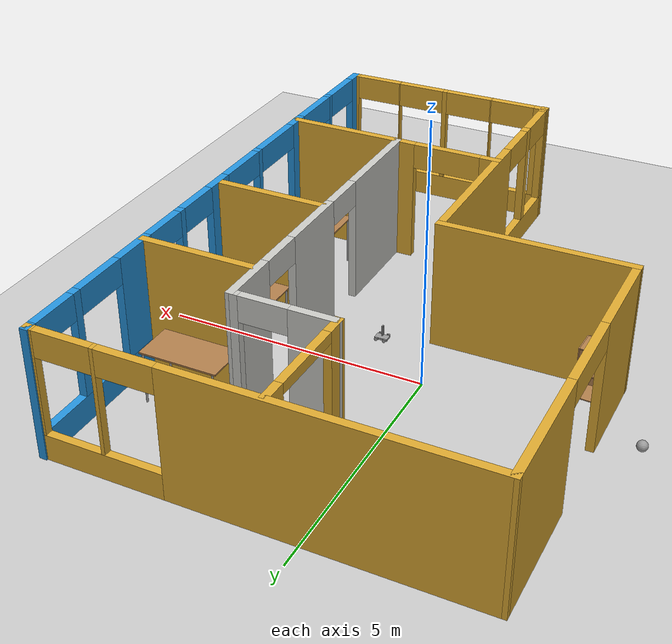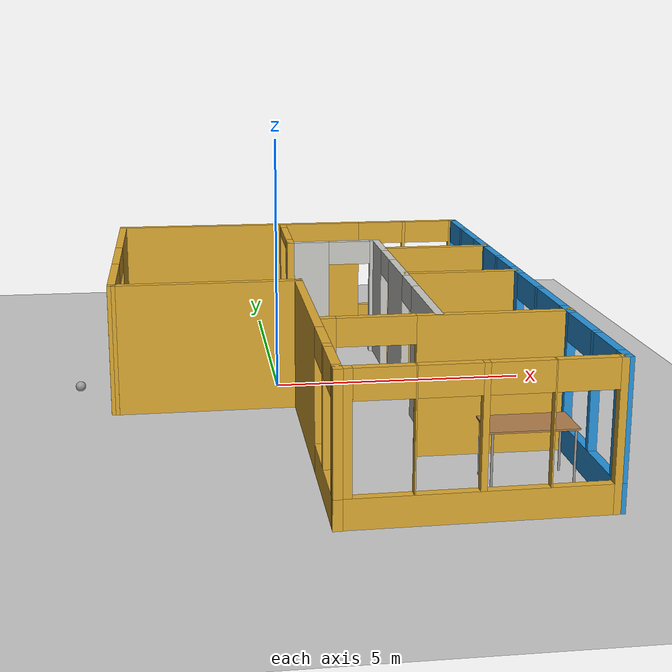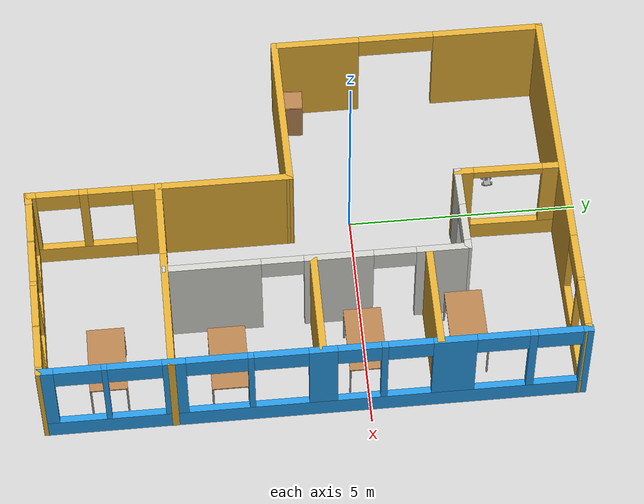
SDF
<sdf version="1.6">
 <world name="default">
  <plugin name="welcomeMessage" filename="libwelcomeMessage.so"/>
  <light name="sun" type="directional">
   <pose>0 0 10 0 -0 0</pose>
   <diffuse>0.8 0.8 0.8 1</diffuse>
   <specular>0.2 0.2 0.2 1</specular>
   <attenuation>
    <range>1000</range>
    <constant>0.9</constant>
    <linear>0.01</linear>
    <quadratic>0.001</quadratic>
   </attenuation>
   <direction>-0.5 0.1 -0.9</direction>
  </light>
  <model name="ground_plane">
   <static>1</static>
   <link name="link">
    <collision name="collision">
     <geometry><plane><normal>0 0 1</normal><size>100 100</size></plane></geometry>
     <surface><friction><ode><mu>100</mu><mu2>50</mu2></ode></friction></surface>
    </collision>
    <visual name="visual">
     <cast_shadows>0</cast_shadows>
     <geometry><plane><normal>0 0 1</normal><size>100 100</size></plane></geometry>
     <material>
      <script><uri>file://media/materials/scripts/gazebo.material</uri><name>Gazebo/Grey</name></script>
     </material>
    </visual>
   </link>
  </model>
  <gravity>0 0 -9.8</gravity>
  <magnetic_field>6e-06 2.3e-05 -4.2e-05</magnetic_field>
  <atmosphere type="adiabatic"/>
  <physics name="default_physics" default="0" type="ode">
   <max_step_size>0.001</max_step_size>
   <real_time_factor>1</real_time_factor>
   <real_time_update_rate>1000</real_time_update_rate>
  </physics>
  <scene><ambient>0.4 0.4 0.4 1</ambient><background>0.7 0.7 0.7 1</background><shadows>1</shadows></scene>
  <spherical_coordinates>
   <surface_model>EARTH_WGS84</surface_model>
   <latitude_deg>0</latitude_deg>
   <longitude_deg>0</longitude_deg>
   <elevation>0</elevation>
   <heading_deg>0</heading_deg>
  </spherical_coordinates>
  <model name="Office_Space">
   <pose>0.73007 -1.18577 0 0 -0 0</pose>
   <link name="Wall_12">
    <pose>-3.91241 2.75125 0 0 0 -1.5708</pose>
    <visual name="Wall_12_Visual_0">
     <pose>-1.78804 0 1.25 0 -0 0</pose>
     <geometry><box><size>2.42393 0.15 2.5</size></box></geometry>
     <material>
      <script><uri>file://media/materials/scripts/gazebo.material</uri><name>Gazebo/Grey</name></script>
      <ambient>0.870588 0.666667 0.192157 1</ambient>
     </material>
     <meta><layer>0</layer></meta>
    </visual>
    <collision name="Wall_12_Collision_0">
     <geometry><box><size>2.42393 0.15 2.5</size></box></geometry>
     <pose>-1.78804 0 1.25 0 -0 0</pose>
    </collision>
    <visual name="Wall_12_Visual_1">
     <pose>2.03212 0 1.25 0 -0 0</pose>
     <geometry><box><size>1.93575 0.15 2.5</size></box></geometry>
     <material>
      <script><uri>file://media/materials/scripts/gazebo.material</uri><name>Gazebo/Grey</name></script>
      <ambient>0.870588 0.666667 0.192157 1</ambient>
     </material>
     <meta><layer>0</layer></meta>
    </visual>
    <collision name="Wall_12_Collision_1">
     <geometry><box><size>1.93575 0.15 2.5</size></box></geometry>
     <pose>2.03212 0 1.25 0 -0 0</pose>
    </collision>
    <visual name="Wall_12_Visual_2">
     <pose>0.24409 0 2.25 0 -0 0</pose>
     <geometry><box><size>1.64032 0.15 0.5</size></box></geometry>
     <material>
      <script><uri>file://media/materials/scripts/gazebo.material</uri><name>Gazebo/Grey</name></script>
      <ambient>0.870588 0.666667 0.192157 1</ambient>
     </material>
     <meta><layer>0</layer></meta>
    </visual>
    <collision name="Wall_12_Collision_2">
     <geometry><box><size>1.64032 0.15 0.5</size></box></geometry>
     <pose>0.24409 0 2.25 0 -0 0</pose>
    </collision>
   </link>
   <link name="Wall_13">
    <collision name="Wall_13_Collision">
     <geometry><box><size>3.6301 0.15 2.5</size></box></geometry>
     <pose>0 0 1.25 0 -0 0</pose>
    </collision>
    <visual name="Wall_13_Visual">
     <pose>0 0 1.25 0 -0 0</pose>
     <geometry><box><size>3.6301 0.15 2.5</size></box></geometry>
     <material>
      <script><uri>file://media/materials/scripts/gazebo.material</uri><name>Gazebo/Grey</name></script>
      <ambient>0.870588 0.666667 0.192157 1</ambient>
     </material>
     <meta><layer>0</layer></meta>
    </visual>
    <pose>-2.17238 -0.153911 0 0 -0 0.0114</pose>
   </link>
   <link name="Wall_14">
    <pose>-0.438951 -2.92746 0 0 0 -1.57317</pose>
    <visual name="Wall_14_Visual_0">
     <pose>-1.14507 0 1.25 0 -0 0</pose>
     <geometry><box><size>3.4202 0.15 2.5</size></box></geometry>
     <material>
      <script><uri>file://media/materials/scripts/gazebo.material</uri><name>Gazebo/Grey</name></script>
      <ambient>0.870588 0.666667 0.192157 1</ambient>
     </material>
     <meta><layer>0</layer></meta>
    </visual>
    <collision name="Wall_14_Collision_0">
     <geometry><box><size>3.4202 0.15 2.5</size></box></geometry>
     <pose>-1.14507 0 1.25 0 -0 0</pose>
    </collision>
    <visual name="Wall_14_Visual_1">
     <pose>1.7101 0 0.25 0 -0 0</pose>
     <geometry><box><size>2.29014 0.15 0.5</size></box></geometry>
     <material>
      <script><uri>file://media/materials/scripts/gazebo.material</uri><name>Gazebo/Grey</name></script>
      <ambient>0.870588 0.666667 0.192157 1</ambient>
     </material>
     <meta><layer>0</layer></meta>
    </visual>
    <collision name="Wall_14_Collision_1">
     <geometry><box><size>2.29014 0.15 0.5</size></box></geometry>
     <pose>1.7101 0 0.25 0 -0 0</pose>
    </collision>
    <visual name="Wall_14_Visual_2">
     <pose>1.60096 0 1.5 0 -0 0</pose>
     <geometry><box><size>0.181862 0.15 2</size></box></geometry>
     <material>
      <script><uri>file://media/materials/scripts/gazebo.material</uri><name>Gazebo/Grey</name></script>
      <ambient>0.870588 0.666667 0.192157 1</ambient>
     </material>
     <meta><layer>0</layer></meta>
    </visual>
    <collision name="Wall_14_Collision_2">
     <geometry><box><size>0.181862 0.15 2</size></box></geometry>
     <pose>1.60096 0 1.5 0 -0 0</pose>
    </collision>
    <visual name="Wall_14_Visual_3">
     <pose>2.73303 0 1.5 0 -0 0</pose>
     <geometry><box><size>0.244282 0.15 2</size></box></geometry>
     <material>
      <script><uri>file://media/materials/scripts/gazebo.material</uri><name>Gazebo/Grey</name></script>
      <ambient>0.870588 0.666667 0.192157 1</ambient>
     </material>
     <meta><layer>0</layer></meta>
    </visual>
    <collision name="Wall_14_Collision_3">
     <geometry><box><size>0.244282 0.15 2</size></box></geometry>
     <pose>2.73303 0 1.5 0 -0 0</pose>
    </collision>
    <visual name="Wall_14_Visual_4">
     <pose>1.03753 0 2.25 0 -0 0</pose>
     <geometry><box><size>0.945 0.15 0.5</size></box></geometry>
     <material>
      <script><uri>file://media/materials/scripts/gazebo.material</uri><name>Gazebo/Grey</name></script>
      <ambient>0.870588 0.666667 0.192157 1</ambient>
     </material>
     <meta><layer>0</layer></meta>
    </visual>
    <collision name="Wall_14_Collision_4">
     <geometry><box><size>0.945 0.15 0.5</size></box></geometry>
     <pose>1.03753 0 2.25 0 -0 0</pose>
    </collision>
    <visual name="Wall_14_Visual_5">
     <pose>2.15139 0 2.25 0 -0 0</pose>
     <geometry><box><size>0.919 0.15 0.5</size></box></geometry>
     <material>
      <script><uri>file://media/materials/scripts/gazebo.material</uri><name>Gazebo/Grey</name></script>
      <ambient>0.870588 0.666667 0.192157 1</ambient>
     </material>
     <meta><layer>0</layer></meta>
    </visual>
    <collision name="Wall_14_Collision_5">
     <geometry><box><size>0.919 0.15 0.5</size></box></geometry>
     <pose>2.15139 0 2.25 0 -0 0</pose>
    </collision>
   </link>
   <link name="Wall_17">
    <pose>1.65872 0.267561 0 0 0 -1.5708</pose>
    <visual name="Wall_17_Visual_0">
     <pose>-2.66794 0 1.25 0 -0 0</pose>
     <geometry><box><size>1.16412 0.15 2.5</size></box></geometry>
     <material>
      <script><uri>file://media/materials/scripts/gazebo.material</uri><name>Gazebo/CeilingTiled</name></script>
      <ambient>0.870588 0.666667 0.192157 1</ambient>
     </material>
     <meta><layer>0</layer></meta>
    </visual>
    <collision name="Wall_17_Collision_0">
     <geometry><box><size>1.16412 0.15 2.5</size></box></geometry>
     <pose>-2.66794 0 1.25 0 -0 0</pose>
    </collision>
    <visual name="Wall_17_Visual_1">
     <pose>-0.452242 0 1.25 0 -0 0</pose>
     <geometry><box><size>1.46728 0.15 2.5</size></box></geometry>
     <material>
      <script><uri>file://media/materials/scripts/gazebo.material</uri><name>Gazebo/CeilingTiled</name></script>
      <ambient>0.870588 0.666667 0.192157 1</ambient>
     </material>
     <meta><layer>0</layer></meta>
    </visual>
    <collision name="Wall_17_Collision_1">
     <geometry><box><size>1.46728 0.15 2.5</size></box></geometry>
     <pose>-0.452242 0 1.25 0 -0 0</pose>
    </collision>
    <visual name="Wall_17_Visual_2">
     <pose>2.2157 0 1.25 0 -0 0</pose>
     <geometry><box><size>2.0686 0.15 2.5</size></box></geometry>
     <material>
      <script><uri>file://media/materials/scripts/gazebo.material</uri><name>Gazebo/CeilingTiled</name></script>
      <ambient>0.870588 0.666667 0.192157 1</ambient>
     </material>
     <meta><layer>0</layer></meta>
    </visual>
    <collision name="Wall_17_Collision_2">
     <geometry><box><size>2.0686 0.15 2.5</size></box></geometry>
     <pose>2.2157 0 1.25 0 -0 0</pose>
    </collision>
    <visual name="Wall_17_Visual_3">
     <pose>-1.63588 0 2.25 0 -0 0</pose>
     <geometry><box><size>0.9 0.15 0.5</size></box></geometry>
     <material>
      <script><uri>file://media/materials/scripts/gazebo.material</uri><name>Gazebo/CeilingTiled</name></script>
      <ambient>0.870588 0.666667 0.192157 1</ambient>
     </material>
     <meta><layer>0</layer></meta>
    </visual>
    <collision name="Wall_17_Collision_3">
     <geometry><box><size>0.9 0.15 0.5</size></box></geometry>
     <pose>-1.63588 0 2.25 0 -0 0</pose>
    </collision>
    <visual name="Wall_17_Visual_4">
     <pose>0.731395 0 2.25 0 -0 0</pose>
     <geometry><box><size>0.9 0.15 0.5</size></box></geometry>
     <material>
      <script><uri>file://media/materials/scripts/gazebo.material</uri><name>Gazebo/CeilingTiled</name></script>
      <ambient>0.870588 0.666667 0.192157 1</ambient>
     </material>
     <meta><layer>0</layer></meta>
    </visual>
    <collision name="Wall_17_Collision_4">
     <geometry><box><size>0.9 0.15 0.5</size></box></geometry>
     <pose>0.731395 0 2.25 0 -0 0</pose>
    </collision>
   </link>
   <link name="Wall_19">
    <pose>0.714749 3.4432 0 0 -0 3.14092</pose>
    <visual name="Wall_19_Visual_0">
     <pose>-0.907152 0 1.25 0 -0 0</pose>
     <geometry><box><size>0.223647 0.15 2.5</size></box></geometry>
     <material>
      <script><uri>file://media/materials/scripts/gazebo.material</uri><name>Gazebo/CeilingTiled</name></script>
      <ambient>0.870588 0.666667 0.192157 1</ambient>
     </material>
     <meta><layer>0</layer></meta>
    </visual>
    <collision name="Wall_19_Collision_0">
     <geometry><box><size>0.223647 0.15 2.5</size></box></geometry>
     <pose>-0.907152 0 1.25 0 -0 0</pose>
    </collision>
    <visual name="Wall_19_Visual_1">
     <pose>0.561824 0 1.25 0 -0 0</pose>
     <geometry><box><size>0.914303 0.15 2.5</size></box></geometry>
     <material>
      <script><uri>file://media/materials/scripts/gazebo.material</uri><name>Gazebo/CeilingTiled</name></script>
      <ambient>0.870588 0.666667 0.192157 1</ambient>
     </material>
     <meta><layer>0</layer></meta>
    </visual>
    <collision name="Wall_19_Collision_1">
     <geometry><box><size>0.914303 0.15 2.5</size></box></geometry>
     <pose>0.561824 0 1.25 0 -0 0</pose>
    </collision>
    <visual name="Wall_19_Visual_2">
     <pose>-0.345328 0 2.25 0 -0 0</pose>
     <geometry><box><size>0.9 0.15 0.5</size></box></geometry>
     <material>
      <script><uri>file://media/materials/scripts/gazebo.material</uri><name>Gazebo/CeilingTiled</name></script>
      <ambient>0.870588 0.666667 0.192157 1</ambient>
     </material>
     <meta><layer>0</layer></meta>
    </visual>
    <collision name="Wall_19_Collision_2">
     <geometry><box><size>0.9 0.15 0.5</size></box></geometry>
     <pose>-0.345328 0 2.25 0 -0 0</pose>
    </collision>
   </link>
   <link name="Wall_21">
    <pose>-0.216001 4.5269 0 0 -0 1.55873</pose>
    <visual name="Wall_21_Visual_0">
     <pose>-0.958077 0 1.25 0 -0 0</pose>
     <geometry><box><size>0.42658 0.15 2.5</size></box></geometry>
     <material>
      <script><uri>file://media/materials/scripts/gazebo.material</uri><name>Gazebo/Grey</name></script>
      <ambient>0.870588 0.666667 0.192157 1</ambient>
     </material>
     <meta><layer>0</layer></meta>
    </visual>
    <collision name="Wall_21_Collision_0">
     <geometry><box><size>0.42658 0.15 2.5</size></box></geometry>
     <pose>-0.958077 0 1.25 0 -0 0</pose>
    </collision>
    <visual name="Wall_21_Visual_1">
     <pose>0.21329 0 0.25 0 -0 0</pose>
     <geometry><box><size>1.91615 0.15 0.5</size></box></geometry>
     <material>
      <script><uri>file://media/materials/scripts/gazebo.material</uri><name>Gazebo/Grey</name></script>
      <ambient>0.870588 0.666667 0.192157 1</ambient>
     </material>
     <meta><layer>0</layer></meta>
    </visual>
    <collision name="Wall_21_Collision_1">
     <geometry><box><size>1.91615 0.15 0.5</size></box></geometry>
     <pose>0.21329 0 0.25 0 -0 0</pose>
    </collision>
    <visual name="Wall_21_Visual_2">
     <pose>0.95029 0 1.5 0 -0 0</pose>
     <geometry><box><size>0.442154 0.15 2</size></box></geometry>
     <material>
      <script><uri>file://media/materials/scripts/gazebo.material</uri><name>Gazebo/Grey</name></script>
      <ambient>0.870588 0.666667 0.192157 1</ambient>
     </material>
     <meta><layer>0</layer></meta>
    </visual>
    <collision name="Wall_21_Collision_2">
     <geometry><box><size>0.442154 0.15 2</size></box></geometry>
     <pose>0.95029 0 1.5 0 -0 0</pose>
    </collision>
    <visual name="Wall_21_Visual_3">
     <pose>-0.007787 0 2.4 0 -0 0</pose>
     <geometry><box><size>1.474 0.15 0.2</size></box></geometry>
     <material>
      <script><uri>file://media/materials/scripts/gazebo.material</uri><name>Gazebo/Grey</name></script>
      <ambient>0.870588 0.666667 0.192157 1</ambient>
     </material>
     <meta><layer>0</layer></meta>
    </visual>
    <collision name="Wall_21_Collision_3">
     <geometry><box><size>1.474 0.15 0.2</size></box></geometry>
     <pose>-0.007787 0 2.4 0 -0 0</pose>
    </collision>
   </link>
   <link name="Wall_23">
    <collision name="Wall_23_Collision">
     <geometry><box><size>2.25 0.15 2.5</size></box></geometry>
     <pose>0 0 1.25 0 -0 0</pose>
    </collision>
    <visual name="Wall_23_Visual">
     <pose>0 0 1.25 0 -0 0</pose>
     <geometry><box><size>2.25 0.15 2.5</size></box></geometry>
     <material>
      <script><uri>file://media/materials/scripts/gazebo.material</uri><name>Gazebo/Grey</name></script>
      <ambient>0.870588 0.666667 0.192157 1</ambient>
     </material>
     <meta><layer>0</layer></meta>
    </visual>
    <pose>2.82349 2.61759 0 0 -0 0</pose>
   </link>
   <link name="Wall_25">
    <collision name="Wall_25_Collision">
     <geometry><box><size>2.25 0.15 2.5</size></box></geometry>
     <pose>0 0 1.25 0 -0 0</pose>
    </collision>
    <visual name="Wall_25_Visual">
     <pose>0 0 1.25 0 -0 0</pose>
     <geometry><box><size>2.25 0.15 2.5</size></box></geometry>
     <material>
      <script><uri>file://media/materials/scripts/gazebo.material</uri><name>Gazebo/Grey</name></script>
      <ambient>0.870588 0.666667 0.192157 1</ambient>
     </material>
     <meta><layer>0</layer></meta>
    </visual>
    <pose>2.78381 0.18419 0 0 -0 0</pose>
   </link>
   <link name="Wall_27">
    <pose>1.73816 -2.93691 0 0 -0 0</pose>
    <visual name="Wall_27_Visual_0">
     <pose>-2.04254 0 1.25 0 -0 0</pose>
     <geometry><box><size>0.414912 0.15 2.5</size></box></geometry>
     <material>
      <script><uri>file://media/materials/scripts/gazebo.material</uri><name>Gazebo/Grey</name></script>
      <ambient>0.870588 0.666667 0.192157 1</ambient>
     </material>
     <meta><layer>0</layer></meta>
    </visual>
    <collision name="Wall_27_Collision_0">
     <geometry><box><size>0.414912 0.15 2.5</size></box></geometry>
     <pose>-2.04254 0 1.25 0 -0 0</pose>
    </collision>
    <visual name="Wall_27_Visual_1">
     <pose>0.888894 0 1.25 0 -0 0</pose>
     <geometry><box><size>2.72221 0.15 2.5</size></box></geometry>
     <material>
      <script><uri>file://media/materials/scripts/gazebo.material</uri><name>Gazebo/Grey</name></script>
      <ambient>0.870588 0.666667 0.192157 1</ambient>
     </material>
     <meta><layer>0</layer></meta>
    </visual>
    <collision name="Wall_27_Collision_1">
     <geometry><box><size>2.72221 0.15 2.5</size></box></geometry>
     <pose>0.888894 0 1.25 0 -0 0</pose>
    </collision>
    <visual name="Wall_27_Visual_2">
     <pose>-1.15365 0 2.25 0 -0 0</pose>
     <geometry><box><size>1.36288 0.15 0.5</size></box></geometry>
     <material>
      <script><uri>file://media/materials/scripts/gazebo.material</uri><name>Gazebo/Grey</name></script>
      <ambient>0.870588 0.666667 0.192157 1</ambient>
     </material>
     <meta><layer>0</layer></meta>
    </visual>
    <collision name="Wall_27_Collision_2">
     <geometry><box><size>1.36288 0.15 0.5</size></box></geometry>
     <pose>-1.15365 0 2.25 0 -0 0</pose>
    </collision>
   </link>
   <link name="Wall_6">
    <pose>-0.002523 5.6788 0 0 -0 0.000652</pose>
    <visual name="Wall_6_Visual_0">
     <pose>-1.18764 0 1.25 0 -0 0</pose>
     <geometry><box><size>5.5945 0.15 2.5</size></box></geometry>
     <material>
      <script><uri>file://media/materials/scripts/gazebo.material</uri><name>Gazebo/Grey</name></script>
      <ambient>0.870588 0.666667 0.192157 1</ambient>
     </material>
     <meta><layer>0</layer></meta>
    </visual>
    <collision name="Wall_6_Collision_0">
     <geometry><box><size>5.5945 0.15 2.5</size></box></geometry>
     <pose>-1.18764 0 1.25 0 -0 0</pose>
    </collision>
    <visual name="Wall_6_Visual_1">
     <pose>2.79725 0 0.25 0 -0 0</pose>
     <geometry><box><size>2.37528 0.15 0.5</size></box></geometry>
     <material>
      <script><uri>file://media/materials/scripts/gazebo.material</uri><name>Gazebo/Grey</name></script>
      <ambient>0.870588 0.666667 0.192157 1</ambient>
     </material>
     <meta><layer>0</layer></meta>
    </visual>
    <collision name="Wall_6_Collision_1">
     <geometry><box><size>2.37528 0.15 0.5</size></box></geometry>
     <pose>2.79725 0 0.25 0 -0 0</pose>
    </collision>
    <visual name="Wall_6_Visual_2">
     <pose>2.69405 0 1.5 0 -0 0</pose>
     <geometry><box><size>0.068884 0.15 2</size></box></geometry>
     <material>
      <script><uri>file://media/materials/scripts/gazebo.material</uri><name>Gazebo/Grey</name></script>
      <ambient>0.870588 0.666667 0.192157 1</ambient>
     </material>
     <meta><layer>0</layer></meta>
    </visual>
    <collision name="Wall_6_Collision_2">
     <geometry><box><size>0.068884 0.15 2</size></box></geometry>
     <pose>2.69405 0 1.5 0 -0 0</pose>
    </collision>
    <visual name="Wall_6_Visual_3">
     <pose>3.88919 0 1.5 0 -0 0</pose>
     <geometry><box><size>0.191396 0.15 2</size></box></geometry>
     <material>
      <script><uri>file://media/materials/scripts/gazebo.material</uri><name>Gazebo/Grey</name></script>
      <ambient>0.870588 0.666667 0.192157 1</ambient>
     </material>
     <meta><layer>0</layer></meta>
    </visual>
    <collision name="Wall_6_Collision_3">
     <geometry><box><size>0.191396 0.15 2</size></box></geometry>
     <pose>3.88919 0 1.5 0 -0 0</pose>
    </collision>
    <visual name="Wall_6_Visual_4">
     <pose>2.13461 0 2.25 0 -0 0</pose>
     <geometry><box><size>1.05 0.15 0.5</size></box></geometry>
     <material>
      <script><uri>file://media/materials/scripts/gazebo.material</uri><name>Gazebo/Grey</name></script>
      <ambient>0.870588 0.666667 0.192157 1</ambient>
     </material>
     <meta><layer>0</layer></meta>
    </visual>
    <collision name="Wall_6_Collision_4">
     <geometry><box><size>1.05 0.15 0.5</size></box></geometry>
     <pose>2.13461 0 2.25 0 -0 0</pose>
    </collision>
    <visual name="Wall_6_Visual_5">
     <pose>3.26099 0 2.25 0 -0 0</pose>
     <geometry><box><size>1.065 0.15 0.5</size></box></geometry>
     <material>
      <script><uri>file://media/materials/scripts/gazebo.material</uri><name>Gazebo/Grey</name></script>
      <ambient>0.870588 0.666667 0.192157 1</ambient>
     </material>
     <meta><layer>0</layer></meta>
    </visual>
    <collision name="Wall_6_Collision_5">
     <geometry><box><size>1.065 0.15 0.5</size></box></geometry>
     <pose>3.26099 0 2.25 0 -0 0</pose>
    </collision>
   </link>
   <link name="Wall_7">
    <pose>3.90736 0.032801 0 0 0 -1.5708</pose>
    <visual name="Wall_7_Visual_0">
     <pose>-5.64293 0 1.25 0 -0 0</pose>
     <geometry><box><size>0.214146 0.15 2.5</size></box></geometry>
     <material>
      <script><uri>file://media/materials/scripts/gazebo.material</uri><name>Gazebo/Grey</name></script>
      <ambient>0.14902 0.584314 0.870588 1</ambient>
     </material>
     <meta><layer>0</layer></meta>
    </visual>
    <collision name="Wall_7_Collision_0">
     <geometry><box><size>0.214146 0.15 2.5</size></box></geometry>
     <pose>-5.64293 0 1.25 0 -0 0</pose>
    </collision>
    <visual name="Wall_7_Visual_1">
     <pose>0.107073 0 0.25 0 -0 0</pose>
     <geometry><box><size>11.2859 0.15 0.5</size></box></geometry>
     <material>
      <script><uri>file://media/materials/scripts/gazebo.material</uri><name>Gazebo/Grey</name></script>
      <ambient>0.14902 0.584314 0.870588 1</ambient>
     </material>
     <meta><layer>0</layer></meta>
    </visual>
    <collision name="Wall_7_Collision_1">
     <geometry><box><size>11.2859 0.15 0.5</size></box></geometry>
     <pose>0.107073 0 0.25 0 -0 0</pose>
    </collision>
    <visual name="Wall_7_Visual_2">
     <pose>-4.50853 0 1.5 0 -0 0</pose>
     <geometry><box><size>0.162645 0.15 2</size></box></geometry>
     <material>
      <script><uri>file://media/materials/scripts/gazebo.material</uri><name>Gazebo/Grey</name></script>
      <ambient>0.14902 0.584314 0.870588 1</ambient>
     </material>
     <meta><layer>0</layer></meta>
    </visual>
    <collision name="Wall_7_Collision_2">
     <geometry><box><size>0.162645 0.15 2</size></box></geometry>
     <pose>-4.50853 0 1.5 0 -0 0</pose>
    </collision>
    <visual name="Wall_7_Visual_3">
     <pose>-2.88275 0 1.5 0 -0 0</pose>
     <geometry><box><size>0.907069 0.15 2</size></box></geometry>
     <material>
      <script><uri>file://media/materials/scripts/gazebo.material</uri><name>Gazebo/Grey</name></script>
      <ambient>0.14902 0.584314 0.870588 1</ambient>
     </material>
     <meta><layer>0</layer></meta>
    </visual>
    <collision name="Wall_7_Collision_3">
     <geometry><box><size>0.907069 0.15 2</size></box></geometry>
     <pose>-2.88275 0 1.5 0 -0 0</pose>
    </collision>
    <visual name="Wall_7_Visual_4">
     <pose>-1.42771 0 1.5 0 -0 0</pose>
     <geometry><box><size>0.139 0.15 2</size></box></geometry>
     <material>
      <script><uri>file://media/materials/scripts/gazebo.material</uri><name>Gazebo/Grey</name></script>
      <ambient>0.14902 0.584314 0.870588 1</ambient>
     </material>
     <meta><layer>0</layer></meta>
    </visual>
    <collision name="Wall_7_Collision_4">
     <geometry><box><size>0.139 0.15 2</size></box></geometry>
     <pose>-1.42771 0 1.5 0 -0 0</pose>
    </collision>
    <visual name="Wall_7_Visual_5">
     <pose>-0.154727 0 1.5 0 -0 0</pose>
     <geometry><box><size>0.594975 0.15 2</size></box></geometry>
     <material>
      <script><uri>file://media/materials/scripts/gazebo.material</uri><name>Gazebo/Grey</name></script>
      <ambient>0.14902 0.584314 0.870588 1</ambient>
     </material>
     <meta><layer>0</layer></meta>
    </visual>
    <collision name="Wall_7_Collision_5">
     <geometry><box><size>0.594975 0.15 2</size></box></geometry>
     <pose>-0.154727 0 1.5 0 -0 0</pose>
    </collision>
    <visual name="Wall_7_Visual_6">
     <pose>1.33715 0 1.5 0 -0 0</pose>
     <geometry><box><size>0.126875 0.15 2</size></box></geometry>
     <material>
      <script><uri>file://media/materials/scripts/gazebo.material</uri><name>Gazebo/Grey</name></script>
      <ambient>0.14902 0.584314 0.870588 1</ambient>
     </material>
     <meta><layer>0</layer></meta>
    </visual>
    <collision name="Wall_7_Collision_6">
     <geometry><box><size>0.126875 0.15 2</size></box></geometry>
     <pose>1.33715 0 1.5 0 -0 0</pose>
    </collision>
    <visual name="Wall_7_Visual_7">
     <pose>2.91697 0 1.5 0 -0 0</pose>
     <geometry><box><size>0.485725 0.15 2</size></box></geometry>
     <material>
      <script><uri>file://media/materials/scripts/gazebo.material</uri><name>Gazebo/Grey</name></script>
      <ambient>0.14902 0.584314 0.870588 1</ambient>
     </material>
     <meta><layer>0</layer></meta>
    </visual>
    <collision name="Wall_7_Collision_7">
     <geometry><box><size>0.485725 0.15 2</size></box></geometry>
     <pose>2.91697 0 1.5 0 -0 0</pose>
    </collision>
    <visual name="Wall_7_Visual_8">
     <pose>4.3453 0 1.5 0 -0 0</pose>
     <geometry><box><size>0.116119 0.15 2</size></box></geometry>
     <material>
      <script><uri>file://media/materials/scripts/gazebo.material</uri><name>Gazebo/Grey</name></script>
      <ambient>0.14902 0.584314 0.870588 1</ambient>
     </material>
     <meta><layer>0</layer></meta>
    </visual>
    <collision name="Wall_7_Collision_8">
     <geometry><box><size>0.116119 0.15 2</size></box></geometry>
     <pose>4.3453 0 1.5 0 -0 0</pose>
    </collision>
    <visual name="Wall_7_Visual_9">
     <pose>5.56918 0 1.5 0 -0 0</pose>
     <geometry><box><size>0.361645 0.15 2</size></box></geometry>
     <material>
      <script><uri>file://media/materials/scripts/gazebo.material</uri><name>Gazebo/Grey</name></script>
      <ambient>0.14902 0.584314 0.870588 1</ambient>
     </material>
     <meta><layer>0</layer></meta>
    </visual>
    <collision name="Wall_7_Collision_9">
     <geometry><box><size>0.361645 0.15 2</size></box></geometry>
     <pose>5.56918 0 1.5 0 -0 0</pose>
    </collision>
    <visual name="Wall_7_Visual_10">
     <pose>-5.06285 0 2.25 0 -0 0</pose>
     <geometry><box><size>0.946 0.15 0.5</size></box></geometry>
     <material>
      <script><uri>file://media/materials/scripts/gazebo.material</uri><name>Gazebo/Grey</name></script>
      <ambient>0.14902 0.584314 0.870588 1</ambient>
     </material>
     <meta><layer>0</layer></meta>
    </visual>
    <collision name="Wall_7_Collision_10">
     <geometry><box><size>0.946 0.15 0.5</size></box></geometry>
     <pose>-5.06285 0 2.25 0 -0 0</pose>
    </collision>
    <visual name="Wall_7_Visual_11">
     <pose>-3.88175 0 2.25 0 -0 0</pose>
     <geometry><box><size>1.09093 0.15 0.5</size></box></geometry>
     <material>
      <script><uri>file://media/materials/scripts/gazebo.material</uri><name>Gazebo/Grey</name></script>
      <ambient>0.14902 0.584314 0.870588 1</ambient>
     </material>
     <meta><layer>0</layer></meta>
    </visual>
    <collision name="Wall_7_Collision_11">
     <geometry><box><size>1.09093 0.15 0.5</size></box></geometry>
     <pose>-3.88175 0 2.25 0 -0 0</pose>
    </collision>
    <visual name="Wall_7_Visual_12">
     <pose>-1.96321 0 2.25 0 -0 0</pose>
     <geometry><box><size>0.932 0.15 0.5</size></box></geometry>
     <material>
      <script><uri>file://media/materials/scripts/gazebo.material</uri><name>Gazebo/Grey</name></script>
      <ambient>0.14902 0.584314 0.870588 1</ambient>
     </material>
     <meta><layer>0</layer></meta>
    </visual>
    <collision name="Wall_7_Collision_12">
     <geometry><box><size>0.932 0.15 0.5</size></box></geometry>
     <pose>-1.96321 0 2.25 0 -0 0</pose>
    </collision>
    <visual name="Wall_7_Visual_13">
     <pose>-0.905214 0 2.25 0 -0 0</pose>
     <geometry><box><size>0.906 0.15 0.5</size></box></geometry>
     <material>
      <script><uri>file://media/materials/scripts/gazebo.material</uri><name>Gazebo/Grey</name></script>
      <ambient>0.14902 0.584314 0.870588 1</ambient>
     </material>
     <meta><layer>0</layer></meta>
    </visual>
    <collision name="Wall_7_Collision_13">
     <geometry><box><size>0.906 0.15 0.5</size></box></geometry>
     <pose>-0.905214 0 2.25 0 -0 0</pose>
    </collision>
    <visual name="Wall_7_Visual_14">
     <pose>0.708236 0 2.25 0 -0 0</pose>
     <geometry><box><size>1.13095 0.15 0.5</size></box></geometry>
     <material>
      <script><uri>file://media/materials/scripts/gazebo.material</uri><name>Gazebo/Grey</name></script>
      <ambient>0.14902 0.584314 0.870588 1</ambient>
     </material>
     <meta><layer>0</layer></meta>
    </visual>
    <collision name="Wall_7_Collision_14">
     <geometry><box><size>1.13095 0.15 0.5</size></box></geometry>
     <pose>0.708236 0 2.25 0 -0 0</pose>
    </collision>
    <visual name="Wall_7_Visual_15">
     <pose>2.03735 0 2.25 0 -0 0</pose>
     <geometry><box><size>1.27353 0.15 0.5</size></box></geometry>
     <material>
      <script><uri>file://media/materials/scripts/gazebo.material</uri><name>Gazebo/Grey</name></script>
      <ambient>0.14902 0.584314 0.870588 1</ambient>
     </material>
     <meta><layer>0</layer></meta>
    </visual>
    <collision name="Wall_7_Collision_15">
     <geometry><box><size>1.27353 0.15 0.5</size></box></geometry>
     <pose>2.03735 0 2.25 0 -0 0</pose>
    </collision>
    <visual name="Wall_7_Visual_16">
     <pose>3.72354 0 2.25 0 -0 0</pose>
     <geometry><box><size>1.1274 0.15 0.5</size></box></geometry>
     <material>
      <script><uri>file://media/materials/scripts/gazebo.material</uri><name>Gazebo/Grey</name></script>
      <ambient>0.14902 0.584314 0.870588 1</ambient>
     </material>
     <meta><layer>0</layer></meta>
    </visual>
    <collision name="Wall_7_Collision_16">
     <geometry><box><size>1.1274 0.15 0.5</size></box></geometry>
     <pose>3.72354 0 2.25 0 -0 0</pose>
    </collision>
    <visual name="Wall_7_Visual_17">
     <pose>4.89586 0 2.25 0 -0 0</pose>
     <geometry><box><size>0.985 0.15 0.5</size></box></geometry>
     <material>
      <script><uri>file://media/materials/scripts/gazebo.material</uri><name>Gazebo/Grey</name></script>
      <ambient>0.14902 0.584314 0.870588 1</ambient>
     </material>
     <meta><layer>0</layer></meta>
    </visual>
    <collision name="Wall_7_Collision_17">
     <geometry><box><size>0.985 0.15 0.5</size></box></geometry>
     <pose>4.89586 0 2.25 0 -0 0</pose>
    </collision>
   </link>
   <link name="Wall_8">
    <pose>1.7309 -5.6683 0 0 0 -3.1296</pose>
    <visual name="Wall_8_Visual_0">
     <pose>-2.15255 0 1.25 0 -0 0</pose>
     <geometry><box><size>0.198543 0.15 2.5</size></box></geometry>
     <material>
      <script><uri>file://media/materials/scripts/gazebo.material</uri><name>Gazebo/Grey</name></script>
      <ambient>0.870588 0.666667 0.192157 1</ambient>
     </material>
     <meta><layer>0</layer></meta>
    </visual>
    <collision name="Wall_8_Collision_0">
     <geometry><box><size>0.198543 0.15 2.5</size></box></geometry>
     <pose>-2.15255 0 1.25 0 -0 0</pose>
    </collision>
    <visual name="Wall_8_Visual_1">
     <pose>0.099272 0 0.25 0 -0 0</pose>
     <geometry><box><size>4.30509 0.15 0.5</size></box></geometry>
     <material>
      <script><uri>file://media/materials/scripts/gazebo.material</uri><name>Gazebo/Grey</name></script>
      <ambient>0.870588 0.666667 0.192157 1</ambient>
     </material>
     <meta><layer>0</layer></meta>
    </visual>
    <collision name="Wall_8_Collision_1">
     <geometry><box><size>4.30509 0.15 0.5</size></box></geometry>
     <pose>0.099272 0 0.25 0 -0 0</pose>
    </collision>
    <visual name="Wall_8_Visual_2">
     <pose>-1.07091 0 1.5 0 -0 0</pose>
     <geometry><box><size>0.020731 0.15 2</size></box></geometry>
     <material>
      <script><uri>file://media/materials/scripts/gazebo.material</uri><name>Gazebo/Grey</name></script>
      <ambient>0.870588 0.666667 0.192157 1</ambient>
     </material>
     <meta><layer>0</layer></meta>
    </visual>
    <collision name="Wall_8_Collision_2">
     <geometry><box><size>0.020731 0.15 2</size></box></geometry>
     <pose>-1.07091 0 1.5 0 -0 0</pose>
    </collision>
    <visual name="Wall_8_Visual_3">
     <pose>-0.025415 0 1.5 0 -0 0</pose>
     <geometry><box><size>0.100258 0.15 2</size></box></geometry>
     <material>
      <script><uri>file://media/materials/scripts/gazebo.material</uri><name>Gazebo/Grey</name></script>
      <ambient>0.870588 0.666667 0.192157 1</ambient>
     </material>
     <meta><layer>0</layer></meta>
    </visual>
    <collision name="Wall_8_Collision_3">
     <geometry><box><size>0.100258 0.15 2</size></box></geometry>
     <pose>-0.025415 0 1.5 0 -0 0</pose>
    </collision>
    <visual name="Wall_8_Visual_4">
     <pose>1.02065 0 1.5 0 -0 0</pose>
     <geometry><box><size>0.021879 0.15 2</size></box></geometry>
     <material>
      <script><uri>file://media/materials/scripts/gazebo.material</uri><name>Gazebo/Grey</name></script>
      <ambient>0.870588 0.666667 0.192157 1</ambient>
     </material>
     <meta><layer>0</layer></meta>
    </visual>
    <collision name="Wall_8_Collision_4">
     <geometry><box><size>0.021879 0.15 2</size></box></geometry>
     <pose>1.02065 0 1.5 0 -0 0</pose>
    </collision>
    <visual name="Wall_8_Visual_5">
     <pose>2.10671 0 1.5 0 -0 0</pose>
     <geometry><box><size>0.290226 0.15 2</size></box></geometry>
     <material>
      <script><uri>file://media/materials/scripts/gazebo.material</uri><name>Gazebo/Grey</name></script>
      <ambient>0.870588 0.666667 0.192157 1</ambient>
     </material>
     <meta><layer>0</layer></meta>
    </visual>
    <collision name="Wall_8_Collision_5">
     <geometry><box><size>0.290226 0.15 2</size></box></geometry>
     <pose>2.10671 0 1.5 0 -0 0</pose>
    </collision>
    <visual name="Wall_8_Visual_6">
     <pose>-1.56728 0 2.25 0 -0 0</pose>
     <geometry><box><size>0.972 0.15 0.5</size></box></geometry>
     <material>
      <script><uri>file://media/materials/scripts/gazebo.material</uri><name>Gazebo/Grey</name></script>
      <ambient>0.870588 0.666667 0.192157 1</ambient>
     </material>
     <meta><layer>0</layer></meta>
    </visual>
    <collision name="Wall_8_Collision_6">
     <geometry><box><size>0.972 0.15 0.5</size></box></geometry>
     <pose>-1.56728 0 2.25 0 -0 0</pose>
    </collision>
    <visual name="Wall_8_Visual_7">
     <pose>-0.568044 0 2.25 0 -0 0</pose>
     <geometry><box><size>0.985 0.15 0.5</size></box></geometry>
     <material>
      <script><uri>file://media/materials/scripts/gazebo.material</uri><name>Gazebo/Grey</name></script>
      <ambient>0.870588 0.666667 0.192157 1</ambient>
     </material>
     <meta><layer>0</layer></meta>
    </visual>
    <collision name="Wall_8_Collision_7">
     <geometry><box><size>0.985 0.15 0.5</size></box></geometry>
     <pose>-0.568044 0 2.25 0 -0 0</pose>
    </collision>
    <visual name="Wall_8_Visual_8">
     <pose>0.517214 0 2.25 0 -0 0</pose>
     <geometry><box><size>0.985 0.15 0.5</size></box></geometry>
     <material>
      <script><uri>file://media/materials/scripts/gazebo.material</uri><name>Gazebo/Grey</name></script>
      <ambient>0.870588 0.666667 0.192157 1</ambient>
     </material>
     <meta><layer>0</layer></meta>
    </visual>
    <collision name="Wall_8_Collision_8">
     <geometry><box><size>0.985 0.15 0.5</size></box></geometry>
     <pose>0.517214 0 2.25 0 -0 0</pose>
    </collision>
    <visual name="Wall_8_Visual_9">
     <pose>1.49659 0 2.25 0 -0 0</pose>
     <geometry><box><size>0.93 0.15 0.5</size></box></geometry>
     <material>
      <script><uri>file://media/materials/scripts/gazebo.material</uri><name>Gazebo/Grey</name></script>
      <ambient>0.870588 0.666667 0.192157 1</ambient>
     </material>
     <meta><layer>0</layer></meta>
    </visual>
    <collision name="Wall_8_Collision_9">
     <geometry><box><size>0.93 0.15 0.5</size></box></geometry>
     <pose>1.49659 0 2.25 0 -0 0</pose>
    </collision>
   </link>
   <static>1</static>
  </model>
  <model name="cabinet">
   <static>1</static>
   <link name="cabinet_bottom_plate">
    <inertial>
     <pose>0 0 -1 0 -0 0</pose>
     <inertia><ixx>2.05</ixx><ixy>0</ixy><ixz>0</ixz><iyy>2.05</iyy><iyz>0</iyz><izz>2.05</izz></inertia>
     <mass>25</mass>
    </inertial>
    <collision name="cabinet_bottom_plate_geom">
     <pose>0 0 0.01 0 -0 0</pose>
     <geometry><box><size>0.45 0.45 0.02</size></box></geometry>
    </collision>
    <visual name="cabinet_bottom_plate_geom_visual">
     <pose>0 0 0.01 0 -0 0</pose>
     <geometry><box><size>0.45 0.45 0.02</size></box></geometry>
     <material>
      <script><uri>file://media/materials/scripts/gazebo.material</uri><name>Gazebo/Wood</name></script>
     </material>
    </visual>
    <collision name="cabinet_bottom_plate_geom_cabinet_back_plate">
     <pose>0.235 0 0.51 0 -0 0</pose>
     <geometry><box><size>0.02 0.45 1.02</size></box></geometry>
    </collision>
    <visual name="cabinet_bottom_plate_geom_cabinet_back_plate_visual">
     <pose>0.235 0 0.51 0 -0 0</pose>
     <geometry><box><size>0.02 0.45 1.02</size></box></geometry>
     <material>
      <script><uri>file://media/materials/scripts/gazebo.material</uri><name>Gazebo/Wood</name></script>
     </material>
    </visual>
    <collision name="cabinet_bottom_plate_geom_cabinet_left_plate">
     <pose>0 0.235 0.51 0 -0 0</pose>
     <geometry><box><size>0.45 0.02 1.02</size></box></geometry>
    </collision>
    <visual name="cabinet_bottom_plate_geom_cabinet_left_plate_visual">
     <pose>0 0.235 0.51 0 -0 0</pose>
     <geometry><box><size>0.45 0.02 1.02</size></box></geometry>
     <material>
      <script><uri>file://media/materials/scripts/gazebo.material</uri><name>Gazebo/Wood</name></script>
     </material>
    </visual>
    <collision name="cabinet_bottom_plate_geom_cabinet_middle_plate">
     <pose>0 0 0.51 0 -0 0</pose>
     <geometry><box><size>0.45 0.45 0.02</size></box></geometry>
    </collision>
    <visual name="cabinet_bottom_plate_geom_cabinet_middle_plate_visual">
     <pose>0 0 0.51 0 -0 0</pose>
     <geometry><box><size>0.45 0.45 0.02</size></box></geometry>
     <material>
      <script><uri>file://media/materials/scripts/gazebo.material</uri><name>Gazebo/Wood</name></script>
     </material>
    </visual>
    <collision name="cabinet_bottom_plate_geom_cabinet_right_plate">
     <pose>0 -0.235 0.51 0 -0 0</pose>
     <geometry><box><size>0.45 0.02 1.02</size></box></geometry>
    </collision>
    <visual name="cabinet_bottom_plate_geom_cabinet_right_plate_visual">
     <pose>0 -0.235 0.51 0 -0 0</pose>
     <geometry><box><size>0.45 0.02 1.02</size></box></geometry>
     <material>
      <script><uri>file://media/materials/scripts/gazebo.material</uri><name>Gazebo/Wood</name></script>
     </material>
    </visual>
    <collision name="cabinet_bottom_plate_geom_cabinet_top_plate">
     <pose>0 0 1.01 0 -0 0</pose>
     <geometry><box><size>0.45 0.45 0.02</size></box></geometry>
    </collision>
    <visual name="cabinet_bottom_plate_geom_cabinet_top_plate_visual">
     <pose>0 0 1.01 0 -0 0</pose>
     <geometry><box><size>0.45 0.45 0.02</size></box></geometry>
     <material>
      <script><uri>file://media/materials/scripts/gazebo.material</uri><name>Gazebo/Wood</name></script>
     </material>
    </visual>
   </link>
   <pose>-2.74866 -1.02239 0 0 0 -1.61952</pose>
  </model>
  <model name="table">
   <static>1</static>
   <link name="link">
    <collision name="surface">
     <pose>0 0 1 0 -0 0</pose>
     <geometry><box><size>1.5 0.8 0.03</size></box></geometry>
     <surface><friction><ode><mu>0.6</mu><mu2>0.6</mu2></ode></friction></surface>
    </collision>
    <visual name="visual1">
     <pose>0 0 1 0 -0 0</pose>
     <geometry><box><size>1.5 0.8 0.03</size></box></geometry>
     <material>
      <script><uri>file://media/materials/scripts/gazebo.material</uri><name>Gazebo/Wood</name></script>
     </material>
    </visual>
    <collision name="front_left_leg">
     <pose>0.68 0.38 0.5 0 -0 0</pose>
     <geometry><cylinder><radius>0.02</radius><length>1</length></cylinder></geometry>
    </collision>
    <visual name="front_left_leg">
     <pose>0.68 0.38 0.5 0 -0 0</pose>
     <geometry><cylinder><radius>0.02</radius><length>1</length></cylinder></geometry>
     <material>
      <script><uri>file://media/materials/scripts/gazebo.material</uri><name>Gazebo/Grey</name></script>
     </material>
    </visual>
    <collision name="front_right_leg">
     <pose>0.68 -0.38 0.5 0 -0 0</pose>
     <geometry><cylinder><radius>0.02</radius><length>1</length></cylinder></geometry>
    </collision>
    <visual name="front_right_leg">
     <pose>0.68 -0.38 0.5 0 -0 0</pose>
     <geometry><cylinder><radius>0.02</radius><length>1</length></cylinder></geometry>
     <material>
      <script><uri>file://media/materials/scripts/gazebo.material</uri><name>Gazebo/Grey</name></script>
     </material>
    </visual>
    <collision name="back_right_leg">
     <pose>-0.68 -0.38 0.5 0 -0 0</pose>
     <geometry><cylinder><radius>0.02</radius><length>1</length></cylinder></geometry>
    </collision>
    <visual name="back_right_leg">
     <pose>-0.68 -0.38 0.5 0 -0 0</pose>
     <geometry><cylinder><radius>0.02</radius><length>1</length></cylinder></geometry>
     <material>
      <script><uri>file://media/materials/scripts/gazebo.material</uri><name>Gazebo/Grey</name></script>
     </material>
    </visual>
    <collision name="back_left_leg">
     <pose>-0.68 0.38 0.5 0 -0 0</pose>
     <geometry><cylinder><radius>0.02</radius><length>1</length></cylinder></geometry>
    </collision>
    <visual name="back_left_leg">
     <pose>-0.68 0.38 0.5 0 -0 0</pose>
     <geometry><cylinder><radius>0.02</radius><length>1</length></cylinder></geometry>
     <material>
      <script><uri>file://media/materials/scripts/gazebo.material</uri><name>Gazebo/Grey</name></script>
     </material>
    </visual>
   </link>
   <pose>3.3286 2.1761 0 0 -0 0</pose>
  </model>
  <model name="table_0">
   <static>1</static>
   <link name="link">
    <collision name="surface">
     <pose>0 0 1 0 -0 0</pose>
     <geometry><box><size>1.5 0.8 0.03</size></box></geometry>
     <surface><friction><ode><mu>0.6</mu><mu2>0.6</mu2></ode></friction></surface>
    </collision>
    <visual name="visual1">
     <pose>0 0 1 0 -0 0</pose>
     <geometry><box><size>1.5 0.8 0.03</size></box></geometry>
     <material>
      <script><uri>file://media/materials/scripts/gazebo.material</uri><name>Gazebo/Wood</name></script>
     </material>
    </visual>
    <collision name="front_left_leg">
     <pose>0.68 0.38 0.5 0 -0 0</pose>
     <geometry><cylinder><radius>0.02</radius><length>1</length></cylinder></geometry>
    </collision>
    <visual name="front_left_leg">
     <pose>0.68 0.38 0.5 0 -0 0</pose>
     <geometry><cylinder><radius>0.02</radius><length>1</length></cylinder></geometry>
     <material>
      <script><uri>file://media/materials/scripts/gazebo.material</uri><name>Gazebo/Grey</name></script>
     </material>
    </visual>
    <collision name="front_right_leg">
     <pose>0.68 -0.38 0.5 0 -0 0</pose>
     <geometry><cylinder><radius>0.02</radius><length>1</length></cylinder></geometry>
    </collision>
    <visual name="front_right_leg">
     <pose>0.68 -0.38 0.5 0 -0 0</pose>
     <geometry><cylinder><radius>0.02</radius><length>1</length></cylinder></geometry>
     <material>
      <script><uri>file://media/materials/scripts/gazebo.material</uri><name>Gazebo/Grey</name></script>
     </material>
    </visual>
    <collision name="back_right_leg">
     <pose>-0.68 -0.38 0.5 0 -0 0</pose>
     <geometry><cylinder><radius>0.02</radius><length>1</length></cylinder></geometry>
    </collision>
    <visual name="back_right_leg">
     <pose>-0.68 -0.38 0.5 0 -0 0</pose>
     <geometry><cylinder><radius>0.02</radius><length>1</length></cylinder></geometry>
     <material>
      <script><uri>file://media/materials/scripts/gazebo.material</uri><name>Gazebo/Grey</name></script>
     </material>
    </visual>
    <collision name="back_left_leg">
     <pose>-0.68 0.38 0.5 0 -0 0</pose>
     <geometry><cylinder><radius>0.02</radius><length>1</length></cylinder></geometry>
    </collision>
    <visual name="back_left_leg">
     <pose>-0.68 0.38 0.5 0 -0 0</pose>
     <geometry><cylinder><radius>0.02</radius><length>1</length></cylinder></geometry>
     <material>
      <script><uri>file://media/materials/scripts/gazebo.material</uri><name>Gazebo/Grey</name></script>
     </material>
    </visual>
   </link>
   <pose>3.56756 -0.010821 0 0 -0 0</pose>
  </model>
  <model name="table_1">
   <static>1</static>
   <link name="link">
    <collision name="surface">
     <pose>0 0 1 0 -0 0</pose>
     <geometry><box><size>1.5 0.8 0.03</size></box></geometry>
     <surface><friction><ode><mu>0.6</mu><mu2>0.6</mu2></ode></friction></surface>
    </collision>
    <visual name="visual1">
     <pose>0 0 1 0 -0 0</pose>
     <geometry><box><size>1.5 0.8 0.03</size></box></geometry>
     <material>
      <script><uri>file://media/materials/scripts/gazebo.material</uri><name>Gazebo/Wood</name></script>
     </material>
    </visual>
    <collision name="front_left_leg">
     <pose>0.68 0.38 0.5 0 -0 0</pose>
     <geometry><cylinder><radius>0.02</radius><length>1</length></cylinder></geometry>
    </collision>
    <visual name="front_left_leg">
     <pose>0.68 0.38 0.5 0 -0 0</pose>
     <geometry><cylinder><radius>0.02</radius><length>1</length></cylinder></geometry>
     <material>
      <script><uri>file://media/materials/scripts/gazebo.material</uri><name>Gazebo/Grey</name></script>
     </material>
    </visual>
    <collision name="front_right_leg">
     <pose>0.68 -0.38 0.5 0 -0 0</pose>
     <geometry><cylinder><radius>0.02</radius><length>1</length></cylinder></geometry>
    </collision>
    <visual name="front_right_leg">
     <pose>0.68 -0.38 0.5 0 -0 0</pose>
     <geometry><cylinder><radius>0.02</radius><length>1</length></cylinder></geometry>
     <material>
      <script><uri>file://media/materials/scripts/gazebo.material</uri><name>Gazebo/Grey</name></script>
     </material>
    </visual>
    <collision name="back_right_leg">
     <pose>-0.68 -0.38 0.5 0 -0 0</pose>
     <geometry><cylinder><radius>0.02</radius><length>1</length></cylinder></geometry>
    </collision>
    <visual name="back_right_leg">
     <pose>-0.68 -0.38 0.5 0 -0 0</pose>
     <geometry><cylinder><radius>0.02</radius><length>1</length></cylinder></geometry>
     <material>
      <script><uri>file://media/materials/scripts/gazebo.material</uri><name>Gazebo/Grey</name></script>
     </material>
    </visual>
    <collision name="back_left_leg">
     <pose>-0.68 0.38 0.5 0 -0 0</pose>
     <geometry><cylinder><radius>0.02</radius><length>1</length></cylinder></geometry>
    </collision>
    <visual name="back_left_leg">
     <pose>-0.68 0.38 0.5 0 -0 0</pose>
     <geometry><cylinder><radius>0.02</radius><length>1</length></cylinder></geometry>
     <material>
      <script><uri>file://media/materials/scripts/gazebo.material</uri><name>Gazebo/Grey</name></script>
     </material>
    </visual>
   </link>
   <pose>3.75589 -2.92152 0 0 -0 0</pose>
  </model>
  <model name="table_2">
   <static>1</static>
   <link name="link">
    <collision name="surface">
     <pose>0 0 1 0 -0 0</pose>
     <geometry><box><size>1.5 0.8 0.03</size></box></geometry>
     <surface><friction><ode><mu>0.6</mu><mu2>0.6</mu2></ode></friction></surface>
    </collision>
    <visual name="visual1">
     <pose>0 0 1 0 -0 0</pose>
     <geometry><box><size>1.5 0.8 0.03</size></box></geometry>
     <material>
      <script><uri>file://media/materials/scripts/gazebo.material</uri><name>Gazebo/Wood</name></script>
     </material>
    </visual>
    <collision name="front_left_leg">
     <pose>0.68 0.38 0.5 0 -0 0</pose>
     <geometry><cylinder><radius>0.02</radius><length>1</length></cylinder></geometry>
    </collision>
    <visual name="front_left_leg">
     <pose>0.68 0.38 0.5 0 -0 0</pose>
     <geometry><cylinder><radius>0.02</radius><length>1</length></cylinder></geometry>
     <material>
      <script><uri>file://media/materials/scripts/gazebo.material</uri><name>Gazebo/Grey</name></script>
     </material>
    </visual>
    <collision name="front_right_leg">
     <pose>0.68 -0.38 0.5 0 -0 0</pose>
     <geometry><cylinder><radius>0.02</radius><length>1</length></cylinder></geometry>
    </collision>
    <visual name="front_right_leg">
     <pose>0.68 -0.38 0.5 0 -0 0</pose>
     <geometry><cylinder><radius>0.02</radius><length>1</length></cylinder></geometry>
     <material>
      <script><uri>file://media/materials/scripts/gazebo.material</uri><name>Gazebo/Grey</name></script>
     </material>
    </visual>
    <collision name="back_right_leg">
     <pose>-0.68 -0.38 0.5 0 -0 0</pose>
     <geometry><cylinder><radius>0.02</radius><length>1</length></cylinder></geometry>
    </collision>
    <visual name="back_right_leg">
     <pose>-0.68 -0.38 0.5 0 -0 0</pose>
     <geometry><cylinder><radius>0.02</radius><length>1</length></cylinder></geometry>
     <material>
      <script><uri>file://media/materials/scripts/gazebo.material</uri><name>Gazebo/Grey</name></script>
     </material>
    </visual>
    <collision name="back_left_leg">
     <pose>-0.68 0.38 0.5 0 -0 0</pose>
     <geometry><cylinder><radius>0.02</radius><length>1</length></cylinder></geometry>
    </collision>
    <visual name="back_left_leg">
     <pose>-0.68 0.38 0.5 0 -0 0</pose>
     <geometry><cylinder><radius>0.02</radius><length>1</length></cylinder></geometry>
     <material>
      <script><uri>file://media/materials/scripts/gazebo.material</uri><name>Gazebo/Grey</name></script>
     </material>
    </visual>
   </link>
   <pose>3.572 -5.47161 0 0 -0 0</pose>
  </model>
  <model name="MRA">
   <link name="link_0">
    <inertial>
     <mass>1</mass>
     <inertia>
      <ixx>0.166667</ixx>
      <ixy>0</ixy>
      <ixz>0</ixz>
      <iyy>0.166667</iyy>
      <iyz>0</iyz>
      <izz>0.166667</izz>
     </inertia>
    </inertial>
    <pose>0.024765 0.00253 -0.04 0 -0 0</pose>
    <visual name="visual">
     <geometry><box><size>0.25 0.15 0.04</size></box></geometry>
     <material>
      <lighting>1</lighting>
      <script><uri>file://media/materials/scripts/gazebo.material</uri><name>Gazebo/Grey</name></script>
      <shader type="pixel"><normal_map>__default__</normal_map></shader>
      <ambient>0.3 0.3 0.3 1</ambient>
      <diffuse>0.7 0.7 0.7 1</diffuse>
      <specular>0.01 0.01 0.01 1</specular>
      <emissive>0 0 0 1</emissive>
     </material>
    </visual>
    <collision name="collision">
     <geometry><box><size>0.25 0.15 0.04</size></box></geometry>
     <surface>
      <friction>
       <ode><mu>1</mu><mu2>1</mu2><fdir1>0 0 0</fdir1><slip1>0</slip1><slip2>0</slip2></ode>
       <torsional>
        <coefficient>1</coefficient>
        <patch_radius>0</patch_radius>
        <surface_radius>0</surface_radius>
        <use_patch_radius>1</use_patch_radius>
        <ode><slip>0</slip></ode>
       </torsional>
      </friction>
      <bounce><restitution_coefficient>0</restitution_coefficient><threshold>1e+06</threshold></bounce>
      <contact>
       <collide_without_contact>0</collide_without_contact>
       <collide_without_contact_bitmask>1</collide_without_contact_bitmask>
       <collide_bitmask>1</collide_bitmask>
       <ode>
        <soft_cfm>0</soft_cfm>
        <soft_erp>0.2</soft_erp>
        <kp>1e+13</kp>
        <kd>1</kd>
        <max_vel>0.01</max_vel>
        <min_depth>0</min_depth>
       </ode>
       <bullet>
        <split_impulse>1</split_impulse>
        <split_impulse_penetration_threshold>-0.01</split_impulse_penetration_threshold>
        <soft_cfm>0</soft_cfm>
        <soft_erp>0.2</soft_erp>
        <kp>1e+13</kp>
        <kd>1</kd>
       </bullet>
      </contact>
     </surface>
    </collision>
   </link>
   <link name="link_1">
    <inertial>
     <mass>1</mass>
     <inertia><ixx>0.145833</ixx><ixy>0</ixy><ixz>0</ixz><iyy>0.145833</iyy><iyz>0</iyz><izz>0.125</izz></inertia>
    </inertial>
    <pose>0.104765 0.10253 -0.04 1.57079 -0 0</pose>
    <visual name="visual">
     <geometry><cylinder><radius>0.035</radius><length>0.03</length></cylinder></geometry>
     <material>
      <lighting>1</lighting>
      <script><uri>file://media/materials/scripts/gazebo.material</uri><name>Gazebo/Grey</name></script>
      <shader type="pixel"><normal_map>__default__</normal_map></shader>
      <ambient>0.3 0.3 0.3 1</ambient>
      <diffuse>0.7 0.7 0.7 1</diffuse>
      <specular>0.01 0.01 0.01 1</specular>
      <emissive>0 0 0 1</emissive>
     </material>
    </visual>
    <collision name="collision">
     <geometry><cylinder><radius>0.035</radius><length>0.03</length></cylinder></geometry>
     <surface>
      <friction>
       <ode><mu>1</mu><mu2>1</mu2><fdir1>0 0 0</fdir1><slip1>0</slip1><slip2>0</slip2></ode>
       <torsional>
        <coefficient>1</coefficient>
        <patch_radius>0</patch_radius>
        <surface_radius>0</surface_radius>
        <use_patch_radius>1</use_patch_radius>
        <ode><slip>0</slip></ode>
       </torsional>
      </friction>
      <bounce><restitution_coefficient>0</restitution_coefficient><threshold>1e+06</threshold></bounce>
      <contact>
       <collide_without_contact>0</collide_without_contact>
       <collide_without_contact_bitmask>1</collide_without_contact_bitmask>
       <collide_bitmask>1</collide_bitmask>
       <ode>
        <soft_cfm>0</soft_cfm>
        <soft_erp>0.2</soft_erp>
        <kp>1e+13</kp>
        <kd>1</kd>
        <max_vel>0.01</max_vel>
        <min_depth>0</min_depth>
       </ode>
       <bullet>
        <split_impulse>1</split_impulse>
        <split_impulse_penetration_threshold>-0.01</split_impulse_penetration_threshold>
        <soft_cfm>0</soft_cfm>
        <soft_erp>0.2</soft_erp>
        <kp>1e+13</kp>
        <kd>1</kd>
       </bullet>
      </contact>
     </surface>
    </collision>
   </link>
   <link name="link_1_clone">
    <inertial>
     <mass>1</mass>
     <inertia><ixx>0.145833</ixx><ixy>0</ixy><ixz>0</ixz><iyy>0.145833</iyy><iyz>0</iyz><izz>0.125</izz></inertia>
    </inertial>
    <pose>-0.055235 0.10253 -0.04 1.57079 -0 0</pose>
    <visual name="visual">
     <geometry><cylinder><radius>0.035</radius><length>0.03</length></cylinder></geometry>
     <material>
      <lighting>1</lighting>
      <script><uri>file://media/materials/scripts/gazebo.material</uri><name>Gazebo/Grey</name></script>
      <shader type="pixel"><normal_map>__default__</normal_map></shader>
      <ambient>0.3 0.3 0.3 1</ambient>
      <diffuse>0.7 0.7 0.7 1</diffuse>
      <specular>0.01 0.01 0.01 1</specular>
      <emissive>0 0 0 1</emissive>
     </material>
    </visual>
    <collision name="collision">
     <geometry><cylinder><radius>0.035</radius><length>0.03</length></cylinder></geometry>
     <surface>
      <friction>
       <ode><mu>1</mu><mu2>1</mu2><fdir1>0 0 0</fdir1><slip1>0</slip1><slip2>0</slip2></ode>
       <torsional>
        <coefficient>1</coefficient>
        <patch_radius>0</patch_radius>
        <surface_radius>0</surface_radius>
        <use_patch_radius>1</use_patch_radius>
        <ode><slip>0</slip></ode>
       </torsional>
      </friction>
      <bounce><restitution_coefficient>0</restitution_coefficient><threshold>1e+06</threshold></bounce>
      <contact>
       <collide_without_contact>0</collide_without_contact>
       <collide_without_contact_bitmask>1</collide_without_contact_bitmask>
       <collide_bitmask>1</collide_bitmask>
       <ode>
        <soft_cfm>0</soft_cfm>
        <soft_erp>0.2</soft_erp>
        <kp>1e+13</kp>
        <kd>1</kd>
        <max_vel>0.01</max_vel>
        <min_depth>0</min_depth>
       </ode>
       <bullet>
        <split_impulse>1</split_impulse>
        <split_impulse_penetration_threshold>-0.01</split_impulse_penetration_threshold>
        <soft_cfm>0</soft_cfm>
        <soft_erp>0.2</soft_erp>
        <kp>1e+13</kp>
        <kd>1</kd>
       </bullet>
      </contact>
     </surface>
    </collision>
   </link>
   <link name="link_1_clone_0">
    <inertial>
     <mass>1</mass>
     <inertia><ixx>0.145833</ixx><ixy>0</ixy><ixz>0</ixz><iyy>0.145833</iyy><iyz>0</iyz><izz>0.125</izz></inertia>
    </inertial>
    <pose>-0.055235 -0.09747 -0.04 1.57079 -0 0</pose>
    <visual name="visual">
     <geometry><cylinder><radius>0.035</radius><length>0.03</length></cylinder></geometry>
     <material>
      <lighting>1</lighting>
      <script><uri>file://media/materials/scripts/gazebo.material</uri><name>Gazebo/Grey</name></script>
      <shader type="pixel"><normal_map>__default__</normal_map></shader>
      <ambient>0.3 0.3 0.3 1</ambient>
      <diffuse>0.7 0.7 0.7 1</diffuse>
      <specular>0.01 0.01 0.01 1</specular>
      <emissive>0 0 0 1</emissive>
     </material>
    </visual>
    <collision name="collision">
     <geometry><cylinder><radius>0.035</radius><length>0.03</length></cylinder></geometry>
     <surface>
      <friction>
       <ode><mu>1</mu><mu2>1</mu2><fdir1>0 0 0</fdir1><slip1>0</slip1><slip2>0</slip2></ode>
       <torsional>
        <coefficient>1</coefficient>
        <patch_radius>0</patch_radius>
        <surface_radius>0</surface_radius>
        <use_patch_radius>1</use_patch_radius>
        <ode><slip>0</slip></ode>
       </torsional>
      </friction>
      <bounce><restitution_coefficient>0</restitution_coefficient><threshold>1e+06</threshold></bounce>
      <contact>
       <collide_without_contact>0</collide_without_contact>
       <collide_without_contact_bitmask>1</collide_without_contact_bitmask>
       <collide_bitmask>1</collide_bitmask>
       <ode>
        <soft_cfm>0</soft_cfm>
        <soft_erp>0.2</soft_erp>
        <kp>1e+13</kp>
        <kd>1</kd>
        <max_vel>0.01</max_vel>
        <min_depth>0</min_depth>
       </ode>
       <bullet>
        <split_impulse>1</split_impulse>
        <split_impulse_penetration_threshold>-0.01</split_impulse_penetration_threshold>
        <soft_cfm>0</soft_cfm>
        <soft_erp>0.2</soft_erp>
        <kp>1e+13</kp>
        <kd>1</kd>
       </bullet>
      </contact>
     </surface>
    </collision>
   </link>
   <link name="link_1_clone_1">
    <inertial>
     <mass>1</mass>
     <inertia><ixx>0.145833</ixx><ixy>0</ixy><ixz>0</ixz><iyy>0.145833</iyy><iyz>0</iyz><izz>0.125</izz></inertia>
    </inertial>
    <pose>0.104765 -0.09747 -0.04 1.57079 -0 0</pose>
    <visual name="visual">
     <geometry><cylinder><radius>0.035</radius><length>0.03</length></cylinder></geometry>
     <material>
      <lighting>1</lighting>
      <script><uri>file://media/materials/scripts/gazebo.material</uri><name>Gazebo/Grey</name></script>
      <shader type="pixel"><normal_map>__default__</normal_map></shader>
      <ambient>0.3 0.3 0.3 1</ambient>
      <diffuse>0.7 0.7 0.7 1</diffuse>
      <specular>0.01 0.01 0.01 1</specular>
      <emissive>0 0 0 1</emissive>
     </material>
    </visual>
    <collision name="collision">
     <geometry><cylinder><radius>0.035</radius><length>0.03</length></cylinder></geometry>
     <surface>
      <friction>
       <ode><mu>1</mu><mu2>1</mu2><fdir1>0 0 0</fdir1><slip1>0</slip1><slip2>0</slip2></ode>
       <torsional>
        <coefficient>1</coefficient>
        <patch_radius>0</patch_radius>
        <surface_radius>0</surface_radius>
        <use_patch_radius>1</use_patch_radius>
        <ode><slip>0</slip></ode>
       </torsional>
      </friction>
      <bounce><restitution_coefficient>0</restitution_coefficient><threshold>1e+06</threshold></bounce>
      <contact>
       <collide_without_contact>0</collide_without_contact>
       <collide_without_contact_bitmask>1</collide_without_contact_bitmask>
       <collide_bitmask>1</collide_bitmask>
       <ode>
        <soft_cfm>0</soft_cfm>
        <soft_erp>0.2</soft_erp>
        <kp>1e+13</kp>
        <kd>1</kd>
        <max_vel>0.01</max_vel>
        <min_depth>0</min_depth>
       </ode>
       <bullet>
        <split_impulse>1</split_impulse>
        <split_impulse_penetration_threshold>-0.01</split_impulse_penetration_threshold>
        <soft_cfm>0</soft_cfm>
        <soft_erp>0.2</soft_erp>
        <kp>1e+13</kp>
        <kd>1</kd>
       </bullet>
      </contact>
     </surface>
    </collision>
   </link>
   <link name="link_2">
    <inertial>
     <mass>1</mass>
     <inertia>
      <ixx>0.166667</ixx>
      <ixy>0</ixy>
      <ixz>0</ixz>
      <iyy>0.166667</iyy>
      <iyz>0</iyz>
      <izz>0.166667</izz>
     </inertia>
    </inertial>
    <pose>0.024765 0.00253 0.1 0 -0 0</pose>
    <visual name="visual">
     <geometry><box><size>0.03 0.03 0.2</size></box></geometry>
     <material>
      <lighting>1</lighting>
      <script><uri>file://media/materials/scripts/gazebo.material</uri><name>Gazebo/Grey</name></script>
      <shader type="pixel"><normal_map>__default__</normal_map></shader>
      <ambient>0.3 0.3 0.3 1</ambient>
      <diffuse>0.7 0.7 0.7 1</diffuse>
      <specular>0.01 0.01 0.01 1</specular>
      <emissive>0 0 0 1</emissive>
     </material>
    </visual>
    <collision name="collision">
     <geometry><box><size>0.03 0.03 0.2</size></box></geometry>
     <surface>
      <friction>
       <ode><mu>1</mu><mu2>1</mu2><fdir1>0 0 0</fdir1><slip1>0</slip1><slip2>0</slip2></ode>
       <torsional>
        <coefficient>1</coefficient>
        <patch_radius>0</patch_radius>
        <surface_radius>0</surface_radius>
        <use_patch_radius>1</use_patch_radius>
        <ode><slip>0</slip></ode>
       </torsional>
      </friction>
      <bounce><restitution_coefficient>0</restitution_coefficient><threshold>1e+06</threshold></bounce>
      <contact>
       <collide_without_contact>0</collide_without_contact>
       <collide_without_contact_bitmask>1</collide_without_contact_bitmask>
       <collide_bitmask>1</collide_bitmask>
       <ode>
        <soft_cfm>0</soft_cfm>
        <soft_erp>0.2</soft_erp>
        <kp>1e+13</kp>
        <kd>1</kd>
        <max_vel>0.01</max_vel>
        <min_depth>0</min_depth>
       </ode>
       <bullet>
        <split_impulse>1</split_impulse>
        <split_impulse_penetration_threshold>-0.01</split_impulse_penetration_threshold>
        <soft_cfm>0</soft_cfm>
        <soft_erp>0.2</soft_erp>
        <kp>1e+13</kp>
        <kd>1</kd>
       </bullet>
      </contact>
     </surface>
    </collision>
   </link>
   <link name="link_2_clone">
    <inertial>
     <mass>1</mass>
     <inertia>
      <ixx>0.166667</ixx>
      <ixy>0</ixy>
      <ixz>0</ixz>
      <iyy>0.166667</iyy>
      <iyz>0</iyz>
      <izz>0.166667</izz>
     </inertia>
    </inertial>
    <pose>0.024765 -0.02747 0.1 0 -0 0</pose>
    <visual name="visual">
     <geometry><box><size>0.03 0.03 0.2</size></box></geometry>
     <material>
      <lighting>1</lighting>
      <script><uri>file://media/materials/scripts/gazebo.material</uri><name>Gazebo/Grey</name></script>
      <shader type="pixel"><normal_map>__default__</normal_map></shader>
      <ambient>0.3 0.3 0.3 1</ambient>
      <diffuse>0.7 0.7 0.7 1</diffuse>
      <specular>0.01 0.01 0.01 1</specular>
      <emissive>0 0 0 1</emissive>
     </material>
    </visual>
    <collision name="collision">
     <geometry><box><size>0.03 0.03 0.2</size></box></geometry>
     <surface>
      <friction>
       <ode><mu>1</mu><mu2>1</mu2><fdir1>0 0 0</fdir1><slip1>0</slip1><slip2>0</slip2></ode>
       <torsional>
        <coefficient>1</coefficient>
        <patch_radius>0</patch_radius>
        <surface_radius>0</surface_radius>
        <use_patch_radius>1</use_patch_radius>
        <ode><slip>0</slip></ode>
       </torsional>
      </friction>
      <bounce><restitution_coefficient>0</restitution_coefficient><threshold>1e+06</threshold></bounce>
      <contact>
       <collide_without_contact>0</collide_without_contact>
       <collide_without_contact_bitmask>1</collide_without_contact_bitmask>
       <collide_bitmask>1</collide_bitmask>
       <ode>
        <soft_cfm>0</soft_cfm>
        <soft_erp>0.2</soft_erp>
        <kp>1e+13</kp>
        <kd>1</kd>
        <max_vel>0.01</max_vel>
        <min_depth>0</min_depth>
       </ode>
       <bullet>
        <split_impulse>1</split_impulse>
        <split_impulse_penetration_threshold>-0.01</split_impulse_penetration_threshold>
        <soft_cfm>0</soft_cfm>
        <soft_erp>0.2</soft_erp>
        <kp>1e+13</kp>
        <kd>1</kd>
       </bullet>
      </contact>
     </surface>
    </collision>
   </link>
   <joint name="link_0_JOINT_0" type="revolute">
    <parent>link_0</parent>
    <child>link_1_clone_1</child>
    <axis>
     <xyz>0 0 1</xyz>
     <use_parent_model_frame>0</use_parent_model_frame>
     <limit>
      <lower>-1.79769e+308</lower>
      <upper>1.79769e+308</upper>
      <effort>-1</effort>
      <velocity>-1</velocity>
     </limit>
     <dynamics>
      <spring_reference>0</spring_reference>
      <spring_stiffness>0</spring_stiffness>
      <damping>0</damping>
     </dynamics>
    </axis>
    <physics>
     <ode><limit><cfm>0</cfm><erp>0.2</erp></limit><suspension><cfm>0</cfm><erp>0.2</erp></suspension></ode>
    </physics>
   </joint>
   <joint name="link_0_JOINT_1" type="revolute">
    <parent>link_0</parent>
    <child>link_1_clone_0</child>
    <axis>
     <xyz>0 0 1</xyz>
     <use_parent_model_frame>0</use_parent_model_frame>
     <limit>
      <lower>-1.79769e+308</lower>
      <upper>1.79769e+308</upper>
      <effort>-1</effort>
      <velocity>-1</velocity>
     </limit>
     <dynamics>
      <spring_reference>0</spring_reference>
      <spring_stiffness>0</spring_stiffness>
      <damping>0</damping>
     </dynamics>
    </axis>
    <physics>
     <ode><limit><cfm>0</cfm><erp>0.2</erp></limit><suspension><cfm>0</cfm><erp>0.2</erp></suspension></ode>
    </physics>
   </joint>
   <joint name="link_0_JOINT_2" type="revolute">
    <parent>link_0</parent>
    <child>link_1</child>
    <axis>
     <xyz>0 0 1</xyz>
     <use_parent_model_frame>0</use_parent_model_frame>
     <limit>
      <lower>-1.79769e+308</lower>
      <upper>1.79769e+308</upper>
      <effort>-1</effort>
      <velocity>-1</velocity>
     </limit>
     <dynamics>
      <spring_reference>0</spring_reference>
      <spring_stiffness>0</spring_stiffness>
      <damping>0</damping>
     </dynamics>
    </axis>
    <physics>
     <ode><limit><cfm>0</cfm><erp>0.2</erp></limit><suspension><cfm>0</cfm><erp>0.2</erp></suspension></ode>
    </physics>
   </joint>
   <joint name="link_0_JOINT_3" type="revolute">
    <parent>link_0</parent>
    <child>link_1_clone</child>
    <axis>
     <xyz>0 0 1</xyz>
     <use_parent_model_frame>0</use_parent_model_frame>
     <limit>
      <lower>-1.79769e+308</lower>
      <upper>1.79769e+308</upper>
      <effort>-1</effort>
      <velocity>-1</velocity>
     </limit>
     <dynamics>
      <spring_reference>0</spring_reference>
      <spring_stiffness>0</spring_stiffness>
      <damping>0</damping>
     </dynamics>
    </axis>
    <physics>
     <ode><limit><cfm>0</cfm><erp>0.2</erp></limit><suspension><cfm>0</cfm><erp>0.2</erp></suspension></ode>
    </physics>
   </joint>
   <joint name="link_0_JOINT_4" type="revolute">
    <parent>link_0</parent>
    <child>link_2</child>
    <pose>0 0 -0.1 0 -0 0</pose>
    <axis>
     <xyz>0 1 0</xyz>
     <use_parent_model_frame>0</use_parent_model_frame>
     <limit>
      <lower>-1.79769e+308</lower>
      <upper>1.79769e+308</upper>
      <effort>-1</effort>
      <velocity>-1</velocity>
     </limit>
     <dynamics>
      <spring_reference>0</spring_reference>
      <spring_stiffness>0</spring_stiffness>
      <damping>0</damping>
     </dynamics>
    </axis>
    <physics>
     <ode><limit><cfm>0</cfm><erp>0.2</erp></limit><suspension><cfm>0</cfm><erp>0.2</erp></suspension></ode>
    </physics>
   </joint>
   <joint name="link_2_JOINT_9" type="revolute">
    <parent>link_2</parent>
    <child>link_2_clone</child>
    <pose>0 0 0.1 0 -0 0</pose>
    <axis>
     <xyz>0 1 0</xyz>
     <use_parent_model_frame>0</use_parent_model_frame>
     <limit>
      <lower>-1.79769e+308</lower>
      <upper>1.79769e+308</upper>
      <effort>-1</effort>
      <velocity>-1</velocity>
     </limit>
     <dynamics>
      <spring_reference>0</spring_reference>
      <spring_stiffness>0</spring_stiffness>
      <damping>0</damping>
     </dynamics>
    </axis>
    <physics>
     <ode><limit><cfm>0</cfm><erp>0.2</erp></limit><suspension><cfm>0</cfm><erp>0.2</erp></suspension></ode>
    </physics>
   </joint>
   <static>0</static>
   <pose>1.19692 -0.995561 0.075 0 1e-06 0.010983</pose>
  </model>
  <model name="MRA_0">
   <link name="link_0">
    <inertial>
     <mass>1</mass>
     <inertia>
      <ixx>0.166667</ixx>
      <ixy>0</ixy>
      <ixz>0</ixz>
      <iyy>0.166667</iyy>
      <iyz>0</iyz>
      <izz>0.166667</izz>
     </inertia>
    </inertial>
    <pose>0.024765 0.00253 -0.04 0 -0 0</pose>
    <visual name="visual">
     <geometry><box><size>0.25 0.15 0.04</size></box></geometry>
     <material>
      <lighting>1</lighting>
      <script><uri>file://media/materials/scripts/gazebo.material</uri><name>Gazebo/Grey</name></script>
      <shader type="pixel"><normal_map>__default__</normal_map></shader>
      <ambient>0.3 0.3 0.3 1</ambient>
      <diffuse>0.7 0.7 0.7 1</diffuse>
      <specular>0.01 0.01 0.01 1</specular>
      <emissive>0 0 0 1</emissive>
     </material>
    </visual>
    <collision name="collision">
     <geometry><box><size>0.25 0.15 0.04</size></box></geometry>
     <surface>
      <friction>
       <ode><mu>1</mu><mu2>1</mu2><fdir1>0 0 0</fdir1><slip1>0</slip1><slip2>0</slip2></ode>
       <torsional>
        <coefficient>1</coefficient>
        <patch_radius>0</patch_radius>
        <surface_radius>0</surface_radius>
        <use_patch_radius>1</use_patch_radius>
        <ode><slip>0</slip></ode>
       </torsional>
      </friction>
      <bounce><restitution_coefficient>0</restitution_coefficient><threshold>1e+06</threshold></bounce>
      <contact>
       <collide_without_contact>0</collide_without_contact>
       <collide_without_contact_bitmask>1</collide_without_contact_bitmask>
       <collide_bitmask>1</collide_bitmask>
       <ode>
        <soft_cfm>0</soft_cfm>
        <soft_erp>0.2</soft_erp>
        <kp>1e+13</kp>
        <kd>1</kd>
        <max_vel>0.01</max_vel>
        <min_depth>0</min_depth>
       </ode>
       <bullet>
        <split_impulse>1</split_impulse>
        <split_impulse_penetration_threshold>-0.01</split_impulse_penetration_threshold>
        <soft_cfm>0</soft_cfm>
        <soft_erp>0.2</soft_erp>
        <kp>1e+13</kp>
        <kd>1</kd>
       </bullet>
      </contact>
     </surface>
    </collision>
   </link>
   <link name="link_1">
    <inertial>
     <mass>1</mass>
     <inertia><ixx>0.145833</ixx><ixy>0</ixy><ixz>0</ixz><iyy>0.145833</iyy><iyz>0</iyz><izz>0.125</izz></inertia>
    </inertial>
    <pose>0.104765 0.10253 -0.04 1.57079 -0 0</pose>
    <visual name="visual">
     <geometry><cylinder><radius>0.035</radius><length>0.03</length></cylinder></geometry>
     <material>
      <lighting>1</lighting>
      <script><uri>file://media/materials/scripts/gazebo.material</uri><name>Gazebo/Grey</name></script>
      <shader type="pixel"><normal_map>__default__</normal_map></shader>
      <ambient>0.3 0.3 0.3 1</ambient>
      <diffuse>0.7 0.7 0.7 1</diffuse>
      <specular>0.01 0.01 0.01 1</specular>
      <emissive>0 0 0 1</emissive>
     </material>
    </visual>
    <collision name="collision">
     <geometry><cylinder><radius>0.035</radius><length>0.03</length></cylinder></geometry>
     <surface>
      <friction>
       <ode><mu>1</mu><mu2>1</mu2><fdir1>0 0 0</fdir1><slip1>0</slip1><slip2>0</slip2></ode>
       <torsional>
        <coefficient>1</coefficient>
        <patch_radius>0</patch_radius>
        <surface_radius>0</surface_radius>
        <use_patch_radius>1</use_patch_radius>
        <ode><slip>0</slip></ode>
       </torsional>
      </friction>
      <bounce><restitution_coefficient>0</restitution_coefficient><threshold>1e+06</threshold></bounce>
      <contact>
       <collide_without_contact>0</collide_without_contact>
       <collide_without_contact_bitmask>1</collide_without_contact_bitmask>
       <collide_bitmask>1</collide_bitmask>
       <ode>
        <soft_cfm>0</soft_cfm>
        <soft_erp>0.2</soft_erp>
        <kp>1e+13</kp>
        <kd>1</kd>
        <max_vel>0.01</max_vel>
        <min_depth>0</min_depth>
       </ode>
       <bullet>
        <split_impulse>1</split_impulse>
        <split_impulse_penetration_threshold>-0.01</split_impulse_penetration_threshold>
        <soft_cfm>0</soft_cfm>
        <soft_erp>0.2</soft_erp>
        <kp>1e+13</kp>
        <kd>1</kd>
       </bullet>
      </contact>
     </surface>
    </collision>
   </link>
   <link name="link_1_clone">
    <inertial>
     <mass>1</mass>
     <inertia><ixx>0.145833</ixx><ixy>0</ixy><ixz>0</ixz><iyy>0.145833</iyy><iyz>0</iyz><izz>0.125</izz></inertia>
    </inertial>
    <pose>-0.055235 0.10253 -0.04 1.57079 -0 0</pose>
    <visual name="visual">
     <geometry><cylinder><radius>0.035</radius><length>0.03</length></cylinder></geometry>
     <material>
      <lighting>1</lighting>
      <script><uri>file://media/materials/scripts/gazebo.material</uri><name>Gazebo/Grey</name></script>
      <shader type="pixel"><normal_map>__default__</normal_map></shader>
      <ambient>0.3 0.3 0.3 1</ambient>
      <diffuse>0.7 0.7 0.7 1</diffuse>
      <specular>0.01 0.01 0.01 1</specular>
      <emissive>0 0 0 1</emissive>
     </material>
    </visual>
    <collision name="collision">
     <geometry><cylinder><radius>0.035</radius><length>0.03</length></cylinder></geometry>
     <surface>
      <friction>
       <ode><mu>1</mu><mu2>1</mu2><fdir1>0 0 0</fdir1><slip1>0</slip1><slip2>0</slip2></ode>
       <torsional>
        <coefficient>1</coefficient>
        <patch_radius>0</patch_radius>
        <surface_radius>0</surface_radius>
        <use_patch_radius>1</use_patch_radius>
        <ode><slip>0</slip></ode>
       </torsional>
      </friction>
      <bounce><restitution_coefficient>0</restitution_coefficient><threshold>1e+06</threshold></bounce>
      <contact>
       <collide_without_contact>0</collide_without_contact>
       <collide_without_contact_bitmask>1</collide_without_contact_bitmask>
       <collide_bitmask>1</collide_bitmask>
       <ode>
        <soft_cfm>0</soft_cfm>
        <soft_erp>0.2</soft_erp>
        <kp>1e+13</kp>
        <kd>1</kd>
        <max_vel>0.01</max_vel>
        <min_depth>0</min_depth>
       </ode>
       <bullet>
        <split_impulse>1</split_impulse>
        <split_impulse_penetration_threshold>-0.01</split_impulse_penetration_threshold>
        <soft_cfm>0</soft_cfm>
        <soft_erp>0.2</soft_erp>
        <kp>1e+13</kp>
        <kd>1</kd>
       </bullet>
      </contact>
     </surface>
    </collision>
   </link>
   <link name="link_1_clone_0">
    <inertial>
     <mass>1</mass>
     <inertia><ixx>0.145833</ixx><ixy>0</ixy><ixz>0</ixz><iyy>0.145833</iyy><iyz>0</iyz><izz>0.125</izz></inertia>
    </inertial>
    <pose>-0.055235 -0.09747 -0.04 1.57079 -0 0</pose>
    <visual name="visual">
     <geometry><cylinder><radius>0.035</radius><length>0.03</length></cylinder></geometry>
     <material>
      <lighting>1</lighting>
      <script><uri>file://media/materials/scripts/gazebo.material</uri><name>Gazebo/Grey</name></script>
      <shader type="pixel"><normal_map>__default__</normal_map></shader>
      <ambient>0.3 0.3 0.3 1</ambient>
      <diffuse>0.7 0.7 0.7 1</diffuse>
      <specular>0.01 0.01 0.01 1</specular>
      <emissive>0 0 0 1</emissive>
     </material>
    </visual>
    <collision name="collision">
     <geometry><cylinder><radius>0.035</radius><length>0.03</length></cylinder></geometry>
     <surface>
      <friction>
       <ode><mu>1</mu><mu2>1</mu2><fdir1>0 0 0</fdir1><slip1>0</slip1><slip2>0</slip2></ode>
       <torsional>
        <coefficient>1</coefficient>
        <patch_radius>0</patch_radius>
        <surface_radius>0</surface_radius>
        <use_patch_radius>1</use_patch_radius>
        <ode><slip>0</slip></ode>
       </torsional>
      </friction>
      <bounce><restitution_coefficient>0</restitution_coefficient><threshold>1e+06</threshold></bounce>
      <contact>
       <collide_without_contact>0</collide_without_contact>
       <collide_without_contact_bitmask>1</collide_without_contact_bitmask>
       <collide_bitmask>1</collide_bitmask>
       <ode>
        <soft_cfm>0</soft_cfm>
        <soft_erp>0.2</soft_erp>
        <kp>1e+13</kp>
        <kd>1</kd>
        <max_vel>0.01</max_vel>
        <min_depth>0</min_depth>
       </ode>
       <bullet>
        <split_impulse>1</split_impulse>
        <split_impulse_penetration_threshold>-0.01</split_impulse_penetration_threshold>
        <soft_cfm>0</soft_cfm>
        <soft_erp>0.2</soft_erp>
        <kp>1e+13</kp>
        <kd>1</kd>
       </bullet>
      </contact>
     </surface>
    </collision>
   </link>
   <link name="link_1_clone_1">
    <inertial>
     <mass>1</mass>
     <inertia><ixx>0.145833</ixx><ixy>0</ixy><ixz>0</ixz><iyy>0.145833</iyy><iyz>0</iyz><izz>0.125</izz></inertia>
    </inertial>
    <pose>0.104765 -0.09747 -0.04 1.57079 -0 0</pose>
    <visual name="visual">
     <geometry><cylinder><radius>0.035</radius><length>0.03</length></cylinder></geometry>
     <material>
      <lighting>1</lighting>
      <script><uri>file://media/materials/scripts/gazebo.material</uri><name>Gazebo/Grey</name></script>
      <shader type="pixel"><normal_map>__default__</normal_map></shader>
      <ambient>0.3 0.3 0.3 1</ambient>
      <diffuse>0.7 0.7 0.7 1</diffuse>
      <specular>0.01 0.01 0.01 1</specular>
      <emissive>0 0 0 1</emissive>
     </material>
    </visual>
    <collision name="collision">
     <geometry><cylinder><radius>0.035</radius><length>0.03</length></cylinder></geometry>
     <surface>
      <friction>
       <ode><mu>1</mu><mu2>1</mu2><fdir1>0 0 0</fdir1><slip1>0</slip1><slip2>0</slip2></ode>
       <torsional>
        <coefficient>1</coefficient>
        <patch_radius>0</patch_radius>
        <surface_radius>0</surface_radius>
        <use_patch_radius>1</use_patch_radius>
        <ode><slip>0</slip></ode>
       </torsional>
      </friction>
      <bounce><restitution_coefficient>0</restitution_coefficient><threshold>1e+06</threshold></bounce>
      <contact>
       <collide_without_contact>0</collide_without_contact>
       <collide_without_contact_bitmask>1</collide_without_contact_bitmask>
       <collide_bitmask>1</collide_bitmask>
       <ode>
        <soft_cfm>0</soft_cfm>
        <soft_erp>0.2</soft_erp>
        <kp>1e+13</kp>
        <kd>1</kd>
        <max_vel>0.01</max_vel>
        <min_depth>0</min_depth>
       </ode>
       <bullet>
        <split_impulse>1</split_impulse>
        <split_impulse_penetration_threshold>-0.01</split_impulse_penetration_threshold>
        <soft_cfm>0</soft_cfm>
        <soft_erp>0.2</soft_erp>
        <kp>1e+13</kp>
        <kd>1</kd>
       </bullet>
      </contact>
     </surface>
    </collision>
   </link>
   <link name="link_2">
    <inertial>
     <mass>1</mass>
     <inertia>
      <ixx>0.166667</ixx>
      <ixy>0</ixy>
      <ixz>0</ixz>
      <iyy>0.166667</iyy>
      <iyz>0</iyz>
      <izz>0.166667</izz>
     </inertia>
    </inertial>
    <pose>0.024765 0.00253 0.1 0 -0 0</pose>
    <visual name="visual">
     <geometry><box><size>0.03 0.03 0.2</size></box></geometry>
     <material>
      <lighting>1</lighting>
      <script><uri>file://media/materials/scripts/gazebo.material</uri><name>Gazebo/Grey</name></script>
      <shader type="pixel"><normal_map>__default__</normal_map></shader>
      <ambient>0.3 0.3 0.3 1</ambient>
      <diffuse>0.7 0.7 0.7 1</diffuse>
      <specular>0.01 0.01 0.01 1</specular>
      <emissive>0 0 0 1</emissive>
     </material>
    </visual>
    <collision name="collision">
     <geometry><box><size>0.03 0.03 0.2</size></box></geometry>
     <surface>
      <friction>
       <ode><mu>1</mu><mu2>1</mu2><fdir1>0 0 0</fdir1><slip1>0</slip1><slip2>0</slip2></ode>
       <torsional>
        <coefficient>1</coefficient>
        <patch_radius>0</patch_radius>
        <surface_radius>0</surface_radius>
        <use_patch_radius>1</use_patch_radius>
        <ode><slip>0</slip></ode>
       </torsional>
      </friction>
      <bounce><restitution_coefficient>0</restitution_coefficient><threshold>1e+06</threshold></bounce>
      <contact>
       <collide_without_contact>0</collide_without_contact>
       <collide_without_contact_bitmask>1</collide_without_contact_bitmask>
       <collide_bitmask>1</collide_bitmask>
       <ode>
        <soft_cfm>0</soft_cfm>
        <soft_erp>0.2</soft_erp>
        <kp>1e+13</kp>
        <kd>1</kd>
        <max_vel>0.01</max_vel>
        <min_depth>0</min_depth>
       </ode>
       <bullet>
        <split_impulse>1</split_impulse>
        <split_impulse_penetration_threshold>-0.01</split_impulse_penetration_threshold>
        <soft_cfm>0</soft_cfm>
        <soft_erp>0.2</soft_erp>
        <kp>1e+13</kp>
        <kd>1</kd>
       </bullet>
      </contact>
     </surface>
    </collision>
   </link>
   <link name="link_2_clone">
    <inertial>
     <mass>1</mass>
     <inertia>
      <ixx>0.166667</ixx>
      <ixy>0</ixy>
      <ixz>0</ixz>
      <iyy>0.166667</iyy>
      <iyz>0</iyz>
      <izz>0.166667</izz>
     </inertia>
    </inertial>
    <pose>0.024765 -0.02747 0.1 0 -0 0</pose>
    <visual name="visual">
     <geometry><box><size>0.03 0.03 0.2</size></box></geometry>
     <material>
      <lighting>1</lighting>
      <script><uri>file://media/materials/scripts/gazebo.material</uri><name>Gazebo/Grey</name></script>
      <shader type="pixel"><normal_map>__default__</normal_map></shader>
      <ambient>0.3 0.3 0.3 1</ambient>
      <diffuse>0.7 0.7 0.7 1</diffuse>
      <specular>0.01 0.01 0.01 1</specular>
      <emissive>0 0 0 1</emissive>
     </material>
    </visual>
    <collision name="collision">
     <geometry><box><size>0.03 0.03 0.2</size></box></geometry>
     <surface>
      <friction>
       <ode><mu>1</mu><mu2>1</mu2><fdir1>0 0 0</fdir1><slip1>0</slip1><slip2>0</slip2></ode>
       <torsional>
        <coefficient>1</coefficient>
        <patch_radius>0</patch_radius>
        <surface_radius>0</surface_radius>
        <use_patch_radius>1</use_patch_radius>
        <ode><slip>0</slip></ode>
       </torsional>
      </friction>
      <bounce><restitution_coefficient>0</restitution_coefficient><threshold>1e+06</threshold></bounce>
      <contact>
       <collide_without_contact>0</collide_without_contact>
       <collide_without_contact_bitmask>1</collide_without_contact_bitmask>
       <collide_bitmask>1</collide_bitmask>
       <ode>
        <soft_cfm>0</soft_cfm>
        <soft_erp>0.2</soft_erp>
        <kp>1e+13</kp>
        <kd>1</kd>
        <max_vel>0.01</max_vel>
        <min_depth>0</min_depth>
       </ode>
       <bullet>
        <split_impulse>1</split_impulse>
        <split_impulse_penetration_threshold>-0.01</split_impulse_penetration_threshold>
        <soft_cfm>0</soft_cfm>
        <soft_erp>0.2</soft_erp>
        <kp>1e+13</kp>
        <kd>1</kd>
       </bullet>
      </contact>
     </surface>
    </collision>
   </link>
   <joint name="link_0_JOINT_0" type="revolute">
    <parent>link_0</parent>
    <child>link_1_clone_1</child>
    <axis>
     <xyz>0 0 1</xyz>
     <use_parent_model_frame>0</use_parent_model_frame>
     <limit>
      <lower>-1.79769e+308</lower>
      <upper>1.79769e+308</upper>
      <effort>-1</effort>
      <velocity>-1</velocity>
     </limit>
     <dynamics>
      <spring_reference>0</spring_reference>
      <spring_stiffness>0</spring_stiffness>
      <damping>0</damping>
     </dynamics>
    </axis>
    <physics>
     <ode><limit><cfm>0</cfm><erp>0.2</erp></limit><suspension><cfm>0</cfm><erp>0.2</erp></suspension></ode>
    </physics>
   </joint>
   <joint name="link_0_JOINT_1" type="revolute">
    <parent>link_0</parent>
    <child>link_1_clone_0</child>
    <axis>
     <xyz>0 0 1</xyz>
     <use_parent_model_frame>0</use_parent_model_frame>
     <limit>
      <lower>-1.79769e+308</lower>
      <upper>1.79769e+308</upper>
      <effort>-1</effort>
      <velocity>-1</velocity>
     </limit>
     <dynamics>
      <spring_reference>0</spring_reference>
      <spring_stiffness>0</spring_stiffness>
      <damping>0</damping>
     </dynamics>
    </axis>
    <physics>
     <ode><limit><cfm>0</cfm><erp>0.2</erp></limit><suspension><cfm>0</cfm><erp>0.2</erp></suspension></ode>
    </physics>
   </joint>
   <joint name="link_0_JOINT_2" type="revolute">
    <parent>link_0</parent>
    <child>link_1</child>
    <axis>
     <xyz>0 0 1</xyz>
     <use_parent_model_frame>0</use_parent_model_frame>
     <limit>
      <lower>-1.79769e+308</lower>
      <upper>1.79769e+308</upper>
      <effort>-1</effort>
      <velocity>-1</velocity>
     </limit>
     <dynamics>
      <spring_reference>0</spring_reference>
      <spring_stiffness>0</spring_stiffness>
      <damping>0</damping>
     </dynamics>
    </axis>
    <physics>
     <ode><limit><cfm>0</cfm><erp>0.2</erp></limit><suspension><cfm>0</cfm><erp>0.2</erp></suspension></ode>
    </physics>
   </joint>
   <joint name="link_0_JOINT_3" type="revolute">
    <parent>link_0</parent>
    <child>link_1_clone</child>
    <axis>
     <xyz>0 0 1</xyz>
     <use_parent_model_frame>0</use_parent_model_frame>
     <limit>
      <lower>-1.79769e+308</lower>
      <upper>1.79769e+308</upper>
      <effort>-1</effort>
      <velocity>-1</velocity>
     </limit>
     <dynamics>
      <spring_reference>0</spring_reference>
      <spring_stiffness>0</spring_stiffness>
      <damping>0</damping>
     </dynamics>
    </axis>
    <physics>
     <ode><limit><cfm>0</cfm><erp>0.2</erp></limit><suspension><cfm>0</cfm><erp>0.2</erp></suspension></ode>
    </physics>
   </joint>
   <joint name="link_0_JOINT_4" type="revolute">
    <parent>link_0</parent>
    <child>link_2</child>
    <pose>0 0 -0.1 0 -0 0</pose>
    <axis>
     <xyz>0 1 0</xyz>
     <use_parent_model_frame>0</use_parent_model_frame>
     <limit>
      <lower>-1.79769e+308</lower>
      <upper>1.79769e+308</upper>
      <effort>-1</effort>
      <velocity>-1</velocity>
     </limit>
     <dynamics>
      <spring_reference>0</spring_reference>
      <spring_stiffness>0</spring_stiffness>
      <damping>0</damping>
     </dynamics>
    </axis>
    <physics>
     <ode><limit><cfm>0</cfm><erp>0.2</erp></limit><suspension><cfm>0</cfm><erp>0.2</erp></suspension></ode>
    </physics>
   </joint>
   <joint name="link_2_JOINT_9" type="revolute">
    <parent>link_2</parent>
    <child>link_2_clone</child>
    <pose>0 0 0.1 0 -0 0</pose>
    <axis>
     <xyz>0 1 0</xyz>
     <use_parent_model_frame>0</use_parent_model_frame>
     <limit>
      <lower>-1.79769e+308</lower>
      <upper>1.79769e+308</upper>
      <effort>-1</effort>
      <velocity>-1</velocity>
     </limit>
     <dynamics>
      <spring_reference>0</spring_reference>
      <spring_stiffness>0</spring_stiffness>
      <damping>0</damping>
     </dynamics>
    </axis>
    <physics>
     <ode><limit><cfm>0</cfm><erp>0.2</erp></limit><suspension><cfm>0</cfm><erp>0.2</erp></suspension></ode>
    </physics>
   </joint>
   <static>0</static>
   <pose>-0.878935 3.15512 0.075001 6e-06 -0 0.010613</pose>
  </model>
  <model name="ball">
   <link name="link_1">
    <inertial>
     <mass>1</mass>
     <inertia><ixx>0.1</ixx><ixy>0</ixy><ixz>0</ixz><iyy>0.1</iyy><iyz>0</iyz><izz>0.1</izz></inertia>
    </inertial>
    <visual name="visual">
     <geometry><sphere><radius>0.1</radius></sphere></geometry>
     <material>
      <lighting>1</lighting>
      <script><uri>file://media/materials/scripts/gazebo.material</uri><name>Gazebo/Grey</name></script>
      <shader type="pixel"><normal_map>__default__</normal_map></shader>
      <ambient>1 1 1 1</ambient>
      <diffuse>1 1 1 1</diffuse>
      <specular>1 1 1 1</specular>
      <emissive>1 1 1 1</emissive>
     </material>
    </visual>
    <collision name="collision">
     <geometry><sphere><radius>0.1</radius></sphere></geometry>
     <surface>
      <friction>
       <ode><mu>1</mu><mu2>1</mu2><fdir1>0 0 0</fdir1><slip1>0</slip1><slip2>0</slip2></ode>
       <torsional>
        <coefficient>1</coefficient>
        <patch_radius>0</patch_radius>
        <surface_radius>0</surface_radius>
        <use_patch_radius>1</use_patch_radius>
        <ode><slip>0</slip></ode>
       </torsional>
      </friction>
      <bounce><restitution_coefficient>0</restitution_coefficient><threshold>1e+06</threshold></bounce>
      <contact>
       <collide_without_contact>0</collide_without_contact>
       <collide_without_contact_bitmask>1</collide_without_contact_bitmask>
       <collide_bitmask>1</collide_bitmask>
       <ode>
        <soft_cfm>0</soft_cfm>
        <soft_erp>0.2</soft_erp>
        <kp>1e+13</kp>
        <kd>1</kd>
        <max_vel>0.01</max_vel>
        <min_depth>0</min_depth>
       </ode>
       <bullet>
        <split_impulse>1</split_impulse>
        <split_impulse_penetration_threshold>-0.01</split_impulse_penetration_threshold>
        <soft_cfm>0</soft_cfm>
        <soft_erp>0.2</soft_erp>
        <kp>1e+13</kp>
        <kd>1</kd>
       </bullet>
      </contact>
     </surface>
    </collision>
   </link>
   <static>0</static>
   <pose>-3.9411 0.104082 0.1 0 -0 0</pose>
  </model>
 </world>
</sdf>
